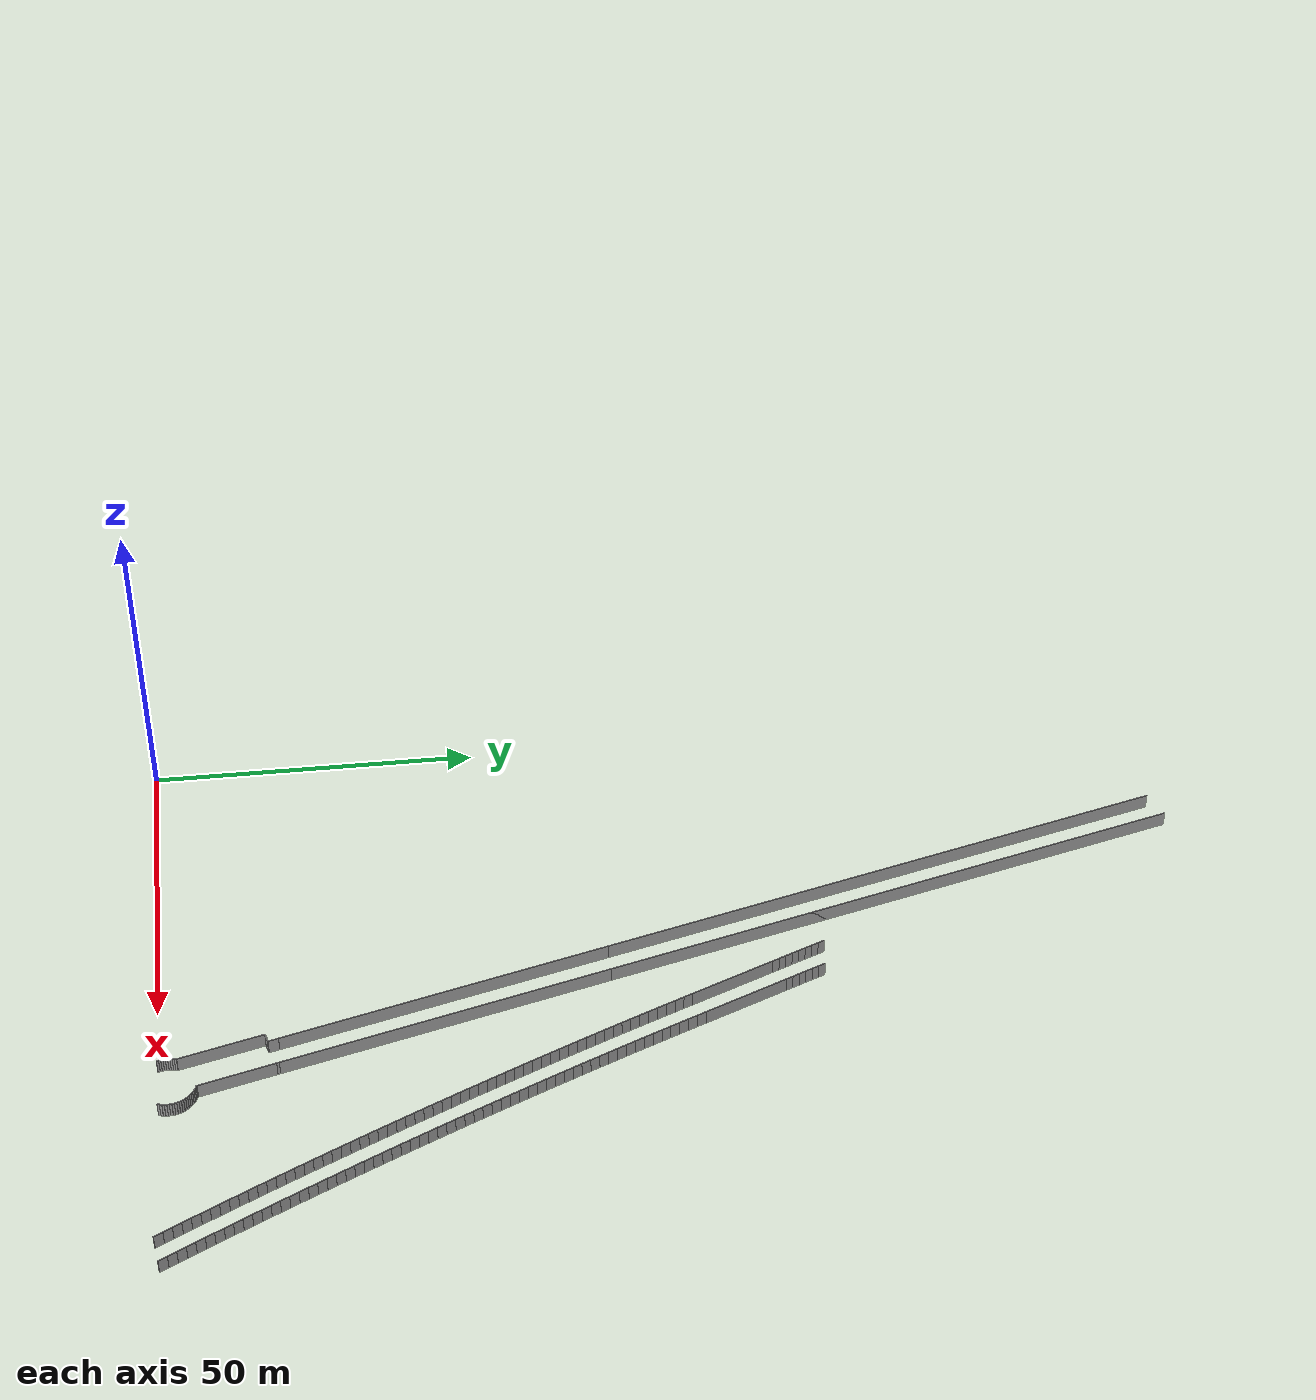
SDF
<?xml version="1.0" ?>
<sdf version="1.6">
  <model name="sps_0207">
    <pose frame="">0 0 0 0 -0 0</pose>
    <static>1</static>
    <self_collide>0</self_collide>
    <allow_auto_disable>0</allow_auto_disable>
    <link name="Wall269">
      <kinematic>0</kinematic>
      <gravity>1</gravity>
      <self_collide>0</self_collide>
      <collision name="collision">
        <geometry>
          <box>
            <size>13.7165 0.15 2.5</size>
          </box>
        </geometry>
        <pose frame="">0 0 0 0 -0 0</pose>
      </collision>
      <visual name="visual">
        <geometry>
          <box>
            <size>13.7165 0.15 2.5</size>
          </box>
        </geometry>
        <pose frame="">0 0 0 0 -0 0</pose>
        <cast_shadows>1</cast_shadows>
        <transparency>0.0</transparency>
      </visual>
      <pose frame="">53.6623 85.8426 1.25 0 0 -1.17761</pose>
    </link>
    <link name="Wall270">
      <kinematic>0</kinematic>
      <gravity>1</gravity>
      <self_collide>0</self_collide>
      <collision name="collision">
        <geometry>
          <box>
            <size>0.404023 0.15 2.5</size>
          </box>
        </geometry>
        <pose frame="">0 0 0 0 -0 0</pose>
      </collision>
      <visual name="visual">
        <geometry>
          <box>
            <size>0.404023 0.15 2.5</size>
          </box>
        </geometry>
        <pose frame="">0 0 0 0 -0 0</pose>
        <cast_shadows>1</cast_shadows>
        <transparency>0.0</transparency>
      </visual>
      <pose frame="">63.4606 17.6979 1.25 0 -0 1.83141</pose>
    </link>
    <link name="Wall271">
      <kinematic>0</kinematic>
      <gravity>1</gravity>
      <self_collide>0</self_collide>
      <collision name="collision">
        <geometry>
          <box>
            <size>51.7473 0.15 2.5</size>
          </box>
        </geometry>
        <pose frame="">0 0 0 0 -0 0</pose>
      </collision>
      <visual name="visual">
        <geometry>
          <box>
            <size>51.7473 0.15 2.5</size>
          </box>
        </geometry>
        <pose frame="">0 0 0 0 -0 0</pose>
        <cast_shadows>1</cast_shadows>
        <transparency>0.0</transparency>
      </visual>
      <pose frame="">56.7417 42.8931 1.25 0 -0 1.83141</pose>
    </link>
    <link name="Wall272">
      <kinematic>0</kinematic>
      <gravity>1</gravity>
      <self_collide>0</self_collide>
      <collision name="collision">
        <geometry>
          <box>
            <size>51.7473 0.15 2.5</size>
          </box>
        </geometry>
        <pose frame="">0 0 0 0 -0 0</pose>
      </collision>
      <visual name="visual">
        <geometry>
          <box>
            <size>51.7473 0.15 2.5</size>
          </box>
        </geometry>
        <pose frame="">0 0 0 0 -0 0</pose>
        <cast_shadows>1</cast_shadows>
        <transparency>0.0</transparency>
      </visual>
      <pose frame="">43.408 92.8931 1.25 0 -0 1.83141</pose>
    </link>
    <link name="Wall329">
      <kinematic>0</kinematic>
      <gravity>1</gravity>
      <self_collide>0</self_collide>
      <collision name="collision">
        <geometry>
          <box>
            <size>1.61069 0.15 2.5</size>
          </box>
        </geometry>
        <pose frame="">0 0 0 0 -0 0</pose>
      </collision>
      <visual name="visual">
        <geometry>
          <box>
            <size>1.61069 0.15 2.5</size>
          </box>
        </geometry>
        <pose frame="">0 0 0 0 -0 0</pose>
        <cast_shadows>1</cast_shadows>
        <transparency>0.0</transparency>
      </visual>
      <pose frame="">58.9327 17.1149 1.25 0 -0 1.83117</pose>
    </link>
    <link name="Wall330">
      <kinematic>0</kinematic>
      <gravity>1</gravity>
      <self_collide>0</self_collide>
      <collision name="collision">
        <geometry>
          <box>
            <size>51.7441 0.15 2.5</size>
          </box>
        </geometry>
        <pose frame="">0 0 0 0 -0 0</pose>
      </collision>
      <visual name="visual">
        <geometry>
          <box>
            <size>51.7441 0.15 2.5</size>
          </box>
        </geometry>
        <pose frame="">0 0 0 0 -0 0</pose>
        <cast_shadows>1</cast_shadows>
        <transparency>0.0</transparency>
      </visual>
      <pose frame="">52.0647 42.8931 1.25 0 -0 1.83117</pose>
    </link>
    <link name="Wall331">
      <kinematic>0</kinematic>
      <gravity>1</gravity>
      <self_collide>0</self_collide>
      <collision name="collision">
        <geometry>
          <box>
            <size>42.4736 0.15 2.5</size>
          </box>
        </geometry>
        <pose frame="">0 0 0 0 -0 0</pose>
      </collision>
      <visual name="visual">
        <geometry>
          <box>
            <size>42.4736 0.15 2.5</size>
          </box>
        </geometry>
        <pose frame="">0 0 0 0 -0 0</pose>
        <cast_shadows>1</cast_shadows>
        <transparency>0.0</transparency>
      </visual>
      <pose frame="">39.9368 88.414 1.25 0 -0 1.83117</pose>
    </link>
    <link name="Wall595">
      <kinematic>0</kinematic>
      <gravity>1</gravity>
      <self_collide>0</self_collide>
      <collision name="collision">
        <geometry>
          <box>
            <size>13.7266 0.15 2.5</size>
          </box>
        </geometry>
        <pose frame="">0 0 0 0 -0 0</pose>
      </collision>
      <visual name="visual">
        <geometry>
          <box>
            <size>13.7266 0.15 2.5</size>
          </box>
        </geometry>
        <pose frame="">0 0 0 0 -0 0</pose>
        <cast_shadows>1</cast_shadows>
        <transparency>0.0</transparency>
      </visual>
      <pose frame="">57.4856 87.4298 1.25 0 -0 1.96409</pose>
    </link>
    <link name="Wall1853">
      <kinematic>0</kinematic>
      <gravity>1</gravity>
      <self_collide>0</self_collide>
      <collision name="collision">
        <geometry>
          <box>
            <size>12.1005 0.15 2.5</size>
          </box>
        </geometry>
        <pose frame="">0 0 0 0 -0 0</pose>
      </collision>
      <visual name="visual">
        <geometry>
          <box>
            <size>12.1005 0.15 2.5</size>
          </box>
        </geometry>
        <pose frame="">0 0 0 0 -0 0</pose>
        <cast_shadows>1</cast_shadows>
        <transparency>0.0</transparency>
      </visual>
      <pose frame="">65.0825 11.6597 1.25 0 0 -1.30832</pose>
    </link>
    <link name="Wall1854">
      <kinematic>0</kinematic>
      <gravity>1</gravity>
      <self_collide>0</self_collide>
      <collision name="collision">
        <geometry>
          <box>
            <size>0.359052 0.15 2.5</size>
          </box>
        </geometry>
        <pose frame="">0 0 0 0 -0 0</pose>
      </collision>
      <visual name="visual">
        <geometry>
          <box>
            <size>0.359052 0.15 2.5</size>
          </box>
        </geometry>
        <pose frame="">0 0 0 0 -0 0</pose>
        <cast_shadows>1</cast_shadows>
        <transparency>0.0</transparency>
      </visual>
      <pose frame="">66.8222 5.75838 1.25 0 0 -0.330674</pose>
    </link>
    <link name="Wall1855">
      <kinematic>0</kinematic>
      <gravity>1</gravity>
      <self_collide>0</self_collide>
      <collision name="collision">
        <geometry>
          <box>
            <size>0.358996 0.15 2.5</size>
          </box>
        </geometry>
        <pose frame="">0 0 0 0 -0 0</pose>
      </collision>
      <visual name="visual">
        <geometry>
          <box>
            <size>0.358996 0.15 2.5</size>
          </box>
        </geometry>
        <pose frame="">0 0 0 0 -0 0</pose>
        <cast_shadows>1</cast_shadows>
        <transparency>0.0</transparency>
      </visual>
      <pose frame="">67.1565 5.6281 1.25 0 0 -0.412683</pose>
    </link>
    <link name="Wall1856">
      <kinematic>0</kinematic>
      <gravity>1</gravity>
      <self_collide>0</self_collide>
      <collision name="collision">
        <geometry>
          <box>
            <size>0.359076 0.15 2.5</size>
          </box>
        </geometry>
        <pose frame="">0 0 0 0 -0 0</pose>
      </collision>
      <visual name="visual">
        <geometry>
          <box>
            <size>0.359076 0.15 2.5</size>
          </box>
        </geometry>
        <pose frame="">0 0 0 0 -0 0</pose>
        <cast_shadows>1</cast_shadows>
        <transparency>0.0</transparency>
      </visual>
      <pose frame="">67.479 5.47099 1.25 0 0 -0.493907</pose>
    </link>
    <link name="Wall1857">
      <kinematic>0</kinematic>
      <gravity>1</gravity>
      <self_collide>0</self_collide>
      <collision name="collision">
        <geometry>
          <box>
            <size>0.359122 0.15 2.5</size>
          </box>
        </geometry>
        <pose frame="">0 0 0 0 -0 0</pose>
      </collision>
      <visual name="visual">
        <geometry>
          <box>
            <size>0.359122 0.15 2.5</size>
          </box>
        </geometry>
        <pose frame="">0 0 0 0 -0 0</pose>
        <cast_shadows>1</cast_shadows>
        <transparency>0.0</transparency>
      </visual>
      <pose frame="">67.7877 5.2881 1.25 0 0 -0.575841</pose>
    </link>
    <link name="Wall1858">
      <kinematic>0</kinematic>
      <gravity>1</gravity>
      <self_collide>0</self_collide>
      <collision name="collision">
        <geometry>
          <box>
            <size>0.35892 0.15 2.5</size>
          </box>
        </geometry>
        <pose frame="">0 0 0 0 -0 0</pose>
      </collision>
      <visual name="visual">
        <geometry>
          <box>
            <size>0.35892 0.15 2.5</size>
          </box>
        </geometry>
        <pose frame="">0 0 0 0 -0 0</pose>
        <cast_shadows>1</cast_shadows>
        <transparency>0.0</transparency>
      </visual>
      <pose frame="">68.0803 5.0807 1.25 0 0 -0.657106</pose>
    </link>
    <link name="Wall1859">
      <kinematic>0</kinematic>
      <gravity>1</gravity>
      <self_collide>0</self_collide>
      <collision name="collision">
        <geometry>
          <box>
            <size>0.359021 0.15 2.5</size>
          </box>
        </geometry>
        <pose frame="">0 0 0 0 -0 0</pose>
      </collision>
      <visual name="visual">
        <geometry>
          <box>
            <size>0.359021 0.15 2.5</size>
          </box>
        </geometry>
        <pose frame="">0 0 0 0 -0 0</pose>
        <cast_shadows>1</cast_shadows>
        <transparency>0.0</transparency>
      </visual>
      <pose frame="">68.355 4.85008 1.25 0 0 -0.739702</pose>
    </link>
    <link name="Wall1860">
      <kinematic>0</kinematic>
      <gravity>1</gravity>
      <self_collide>0</self_collide>
      <collision name="collision">
        <geometry>
          <box>
            <size>0.358995 0.15 2.5</size>
          </box>
        </geometry>
        <pose frame="">0 0 0 0 -0 0</pose>
      </collision>
      <visual name="visual">
        <geometry>
          <box>
            <size>0.358995 0.15 2.5</size>
          </box>
        </geometry>
        <pose frame="">0 0 0 0 -0 0</pose>
        <cast_shadows>1</cast_shadows>
        <transparency>0.0</transparency>
      </visual>
      <pose frame="">68.61 4.59779 1.25 0 0 -0.820389</pose>
    </link>
    <link name="Wall1861">
      <kinematic>0</kinematic>
      <gravity>1</gravity>
      <self_collide>0</self_collide>
      <collision name="collision">
        <geometry>
          <box>
            <size>0.359109 0.15 2.5</size>
          </box>
        </geometry>
        <pose frame="">0 0 0 0 -0 0</pose>
      </collision>
      <visual name="visual">
        <geometry>
          <box>
            <size>0.359109 0.15 2.5</size>
          </box>
        </geometry>
        <pose frame="">0 0 0 0 -0 0</pose>
        <cast_shadows>1</cast_shadows>
        <transparency>0.0</transparency>
      </visual>
      <pose frame="">68.8437 4.32561 1.25 0 0 -0.90224</pose>
    </link>
    <link name="Wall1862">
      <kinematic>0</kinematic>
      <gravity>1</gravity>
      <self_collide>0</self_collide>
      <collision name="collision">
        <geometry>
          <box>
            <size>0.359062 0.15 2.5</size>
          </box>
        </geometry>
        <pose frame="">0 0 0 0 -0 0</pose>
      </collision>
      <visual name="visual">
        <geometry>
          <box>
            <size>0.359062 0.15 2.5</size>
          </box>
        </geometry>
        <pose frame="">0 0 0 0 -0 0</pose>
        <cast_shadows>1</cast_shadows>
        <transparency>0.0</transparency>
      </visual>
      <pose frame="">69.0544 4.0352 1.25 0 0 -0.984067</pose>
    </link>
    <link name="Wall1863">
      <kinematic>0</kinematic>
      <gravity>1</gravity>
      <self_collide>0</self_collide>
      <collision name="collision">
        <geometry>
          <box>
            <size>0.358927 0.15 2.5</size>
          </box>
        </geometry>
        <pose frame="">0 0 0 0 -0 0</pose>
      </collision>
      <visual name="visual">
        <geometry>
          <box>
            <size>0.358927 0.15 2.5</size>
          </box>
        </geometry>
        <pose frame="">0 0 0 0 -0 0</pose>
        <cast_shadows>1</cast_shadows>
        <transparency>0.0</transparency>
      </visual>
      <pose frame="">69.2407 3.72868 1.25 0 0 -1.06523</pose>
    </link>
    <link name="Wall1864">
      <kinematic>0</kinematic>
      <gravity>1</gravity>
      <self_collide>0</self_collide>
      <collision name="collision">
        <geometry>
          <box>
            <size>0.359119 0.15 2.5</size>
          </box>
        </geometry>
        <pose frame="">0 0 0 0 -0 0</pose>
      </collision>
      <visual name="visual">
        <geometry>
          <box>
            <size>0.359119 0.15 2.5</size>
          </box>
        </geometry>
        <pose frame="">0 0 0 0 -0 0</pose>
        <cast_shadows>1</cast_shadows>
        <transparency>0.0</transparency>
      </visual>
      <pose frame="">69.4015 3.40797 1.25 0 0 -1.14729</pose>
    </link>
    <link name="Wall1865">
      <kinematic>0</kinematic>
      <gravity>1</gravity>
      <self_collide>0</self_collide>
      <collision name="collision">
        <geometry>
          <box>
            <size>0.359057 0.15 2.5</size>
          </box>
        </geometry>
        <pose frame="">0 0 0 0 -0 0</pose>
      </collision>
      <visual name="visual">
        <geometry>
          <box>
            <size>0.359057 0.15 2.5</size>
          </box>
        </geometry>
        <pose frame="">0 0 0 0 -0 0</pose>
        <cast_shadows>1</cast_shadows>
        <transparency>0.0</transparency>
      </visual>
      <pose frame="">69.5355 3.07518 1.25 0 0 -1.22824</pose>
    </link>
    <link name="Wall1866">
      <kinematic>0</kinematic>
      <gravity>1</gravity>
      <self_collide>0</self_collide>
      <collision name="collision">
        <geometry>
          <box>
            <size>0.359079 0.15 2.5</size>
          </box>
        </geometry>
        <pose frame="">0 0 0 0 -0 0</pose>
      </collision>
      <visual name="visual">
        <geometry>
          <box>
            <size>0.359079 0.15 2.5</size>
          </box>
        </geometry>
        <pose frame="">0 0 0 0 -0 0</pose>
        <cast_shadows>1</cast_shadows>
        <transparency>0.0</transparency>
      </visual>
      <pose frame="">69.6421 2.73259 1.25 0 0 -1.31052</pose>
    </link>
    <link name="Wall1867">
      <kinematic>0</kinematic>
      <gravity>1</gravity>
      <self_collide>0</self_collide>
      <collision name="collision">
        <geometry>
          <box>
            <size>0.359147 0.15 2.5</size>
          </box>
        </geometry>
        <pose frame="">0 0 0 0 -0 0</pose>
      </collision>
      <visual name="visual">
        <geometry>
          <box>
            <size>0.359147 0.15 2.5</size>
          </box>
        </geometry>
        <pose frame="">0 0 0 0 -0 0</pose>
        <cast_shadows>1</cast_shadows>
        <transparency>0.0</transparency>
      </visual>
      <pose frame="">69.7203 2.3824 1.25 0 0 -1.39157</pose>
    </link>
    <link name="Wall1868">
      <kinematic>0</kinematic>
      <gravity>1</gravity>
      <self_collide>0</self_collide>
      <collision name="collision">
        <geometry>
          <box>
            <size>0.359111 0.15 2.5</size>
          </box>
        </geometry>
        <pose frame="">0 0 0 0 -0 0</pose>
      </collision>
      <visual name="visual">
        <geometry>
          <box>
            <size>0.359111 0.15 2.5</size>
          </box>
        </geometry>
        <pose frame="">0 0 0 0 -0 0</pose>
        <cast_shadows>1</cast_shadows>
        <transparency>0.0</transparency>
      </visual>
      <pose frame="">69.7697 2.02699 1.25 0 0 -1.47377</pose>
    </link>
    <link name="Wall1869">
      <kinematic>0</kinematic>
      <gravity>1</gravity>
      <self_collide>0</self_collide>
      <collision name="collision">
        <geometry>
          <box>
            <size>0.359053 0.15 2.5</size>
          </box>
        </geometry>
        <pose frame="">0 0 0 0 -0 0</pose>
      </collision>
      <visual name="visual">
        <geometry>
          <box>
            <size>0.359053 0.15 2.5</size>
          </box>
        </geometry>
        <pose frame="">0 0 0 0 -0 0</pose>
        <cast_shadows>1</cast_shadows>
        <transparency>0.0</transparency>
      </visual>
      <pose frame="">69.7899 1.66878 1.25 0 0 -1.55516</pose>
    </link>
    <link name="Wall1870">
      <kinematic>0</kinematic>
      <gravity>1</gravity>
      <self_collide>0</self_collide>
      <collision name="collision">
        <geometry>
          <box>
            <size>0.358944 0.15 2.5</size>
          </box>
        </geometry>
        <pose frame="">0 0 0 0 -0 0</pose>
      </collision>
      <visual name="visual">
        <geometry>
          <box>
            <size>0.358944 0.15 2.5</size>
          </box>
        </geometry>
        <pose frame="">0 0 0 0 -0 0</pose>
        <cast_shadows>1</cast_shadows>
        <transparency>0.0</transparency>
      </visual>
      <pose frame="">69.7808 1.31019 1.25 0 0 -1.63716</pose>
    </link>
    <link name="Wall1871">
      <kinematic>0</kinematic>
      <gravity>1</gravity>
      <self_collide>0</self_collide>
      <collision name="collision">
        <geometry>
          <box>
            <size>0.359136 0.15 2.5</size>
          </box>
        </geometry>
        <pose frame="">0 0 0 0 -0 0</pose>
      </collision>
      <visual name="visual">
        <geometry>
          <box>
            <size>0.359136 0.15 2.5</size>
          </box>
        </geometry>
        <pose frame="">0 0 0 0 -0 0</pose>
        <cast_shadows>1</cast_shadows>
        <transparency>0.0</transparency>
      </visual>
      <pose frame="">69.7425 0.953505 1.25 0 0 -1.71851</pose>
    </link>
    <link name="Wall1872">
      <kinematic>0</kinematic>
      <gravity>1</gravity>
      <self_collide>0</self_collide>
      <collision name="collision">
        <geometry>
          <box>
            <size>0.358993 0.15 2.5</size>
          </box>
        </geometry>
        <pose frame="">0 0 0 0 -0 0</pose>
      </collision>
      <visual name="visual">
        <geometry>
          <box>
            <size>0.358993 0.15 2.5</size>
          </box>
        </geometry>
        <pose frame="">0 0 0 0 -0 0</pose>
        <cast_shadows>1</cast_shadows>
        <transparency>0.0</transparency>
      </visual>
      <pose frame="">69.6753 0.601088 1.25 0 0 -1.79994</pose>
    </link>
    <link name="Wall1873">
      <kinematic>0</kinematic>
      <gravity>1</gravity>
      <self_collide>0</self_collide>
      <collision name="collision">
        <geometry>
          <box>
            <size>0.359076 0.15 2.5</size>
          </box>
        </geometry>
        <pose frame="">0 0 0 0 -0 0</pose>
      </collision>
      <visual name="visual">
        <geometry>
          <box>
            <size>0.359076 0.15 2.5</size>
          </box>
        </geometry>
        <pose frame="">0 0 0 0 -0 0</pose>
        <cast_shadows>1</cast_shadows>
        <transparency>0.0</transparency>
      </visual>
      <pose frame="">69.5795 0.255385 1.25 0 0 -1.88228</pose>
    </link>
    <link name="Wall1900">
      <kinematic>0</kinematic>
      <gravity>1</gravity>
      <self_collide>0</self_collide>
      <collision name="collision">
        <geometry>
          <box>
            <size>0.335259 0.15 2.5</size>
          </box>
        </geometry>
        <pose frame="">0 0 0 0 -0 0</pose>
      </collision>
      <visual name="visual">
        <geometry>
          <box>
            <size>0.335259 0.15 2.5</size>
          </box>
        </geometry>
        <pose frame="">0 0 0 0 -0 0</pose>
        <cast_shadows>1</cast_shadows>
        <transparency>0.0</transparency>
      </visual>
      <pose frame="">61.2461 0.148513 1.25 0 -0 1.90775</pose>
    </link>
    <link name="Wall1901">
      <kinematic>0</kinematic>
      <gravity>1</gravity>
      <self_collide>0</self_collide>
      <collision name="collision">
        <geometry>
          <box>
            <size>0.335064 0.15 2.5</size>
          </box>
        </geometry>
        <pose frame="">0 0 0 0 -0 0</pose>
      </collision>
      <visual name="visual">
        <geometry>
          <box>
            <size>0.335064 0.15 2.5</size>
          </box>
        </geometry>
        <pose frame="">0 0 0 0 -0 0</pose>
        <cast_shadows>1</cast_shadows>
        <transparency>0.0</transparency>
      </visual>
      <pose frame="">61.1475 0.468612 1.25 0 -0 1.83093</pose>
    </link>
    <link name="Wall1902">
      <kinematic>0</kinematic>
      <gravity>1</gravity>
      <self_collide>0</self_collide>
      <collision name="collision">
        <geometry>
          <box>
            <size>0.33526 0.15 2.5</size>
          </box>
        </geometry>
        <pose frame="">0 0 0 0 -0 0</pose>
      </collision>
      <visual name="visual">
        <geometry>
          <box>
            <size>0.33526 0.15 2.5</size>
          </box>
        </geometry>
        <pose frame="">0 0 0 0 -0 0</pose>
        <cast_shadows>1</cast_shadows>
        <transparency>0.0</transparency>
      </visual>
      <pose frame="">61.0738 0.795302 1.25 0 -0 1.75498</pose>
    </link>
    <link name="Wall1903">
      <kinematic>0</kinematic>
      <gravity>1</gravity>
      <self_collide>0</self_collide>
      <collision name="collision">
        <geometry>
          <box>
            <size>0.335131 0.15 2.5</size>
          </box>
        </geometry>
        <pose frame="">0 0 0 0 -0 0</pose>
      </collision>
      <visual name="visual">
        <geometry>
          <box>
            <size>0.335131 0.15 2.5</size>
          </box>
        </geometry>
        <pose frame="">0 0 0 0 -0 0</pose>
        <cast_shadows>1</cast_shadows>
        <transparency>0.0</transparency>
      </visual>
      <pose frame="">61.025 1.12669 1.25 0 -0 1.67846</pose>
    </link>
    <link name="Wall1904">
      <kinematic>0</kinematic>
      <gravity>1</gravity>
      <self_collide>0</self_collide>
      <collision name="collision">
        <geometry>
          <box>
            <size>0.335379 0.15 2.5</size>
          </box>
        </geometry>
        <pose frame="">0 0 0 0 -0 0</pose>
      </collision>
      <visual name="visual">
        <geometry>
          <box>
            <size>0.335379 0.15 2.5</size>
          </box>
        </geometry>
        <pose frame="">0 0 0 0 -0 0</pose>
        <cast_shadows>1</cast_shadows>
        <transparency>0.0</transparency>
      </visual>
      <pose frame="">61.0016 1.46089 1.25 0 -0 1.60301</pose>
    </link>
    <link name="Wall1905">
      <kinematic>0</kinematic>
      <gravity>1</gravity>
      <self_collide>0</self_collide>
      <collision name="collision">
        <geometry>
          <box>
            <size>0.335114 0.15 2.5</size>
          </box>
        </geometry>
        <pose frame="">0 0 0 0 -0 0</pose>
      </collision>
      <visual name="visual">
        <geometry>
          <box>
            <size>0.335114 0.15 2.5</size>
          </box>
        </geometry>
        <pose frame="">0 0 0 0 -0 0</pose>
        <cast_shadows>1</cast_shadows>
        <transparency>0.0</transparency>
      </visual>
      <pose frame="">61.0037 1.79588 1.25 0 -0 1.52598</pose>
    </link>
    <link name="Wall1906">
      <kinematic>0</kinematic>
      <gravity>1</gravity>
      <self_collide>0</self_collide>
      <collision name="collision">
        <geometry>
          <box>
            <size>0.335268 0.15 2.5</size>
          </box>
        </geometry>
        <pose frame="">0 0 0 0 -0 0</pose>
      </collision>
      <visual name="visual">
        <geometry>
          <box>
            <size>0.335268 0.15 2.5</size>
          </box>
        </geometry>
        <pose frame="">0 0 0 0 -0 0</pose>
        <cast_shadows>1</cast_shadows>
        <transparency>0.0</transparency>
      </visual>
      <pose frame="">61.0315 2.12968 1.25 0 -0 1.44999</pose>
    </link>
    <link name="Wall1907">
      <kinematic>0</kinematic>
      <gravity>1</gravity>
      <self_collide>0</self_collide>
      <collision name="collision">
        <geometry>
          <box>
            <size>0.335279 0.15 2.5</size>
          </box>
        </geometry>
        <pose frame="">0 0 0 0 -0 0</pose>
      </collision>
      <visual name="visual">
        <geometry>
          <box>
            <size>0.335279 0.15 2.5</size>
          </box>
        </geometry>
        <pose frame="">0 0 0 0 -0 0</pose>
        <cast_shadows>1</cast_shadows>
        <transparency>0.0</transparency>
      </visual>
      <pose frame="">61.0845 2.46049 1.25 0 -0 1.37383</pose>
    </link>
    <link name="Wall1908">
      <kinematic>0</kinematic>
      <gravity>1</gravity>
      <self_collide>0</self_collide>
      <collision name="collision">
        <geometry>
          <box>
            <size>0.335232 0.15 2.5</size>
          </box>
        </geometry>
        <pose frame="">0 0 0 0 -0 0</pose>
      </collision>
      <visual name="visual">
        <geometry>
          <box>
            <size>0.335232 0.15 2.5</size>
          </box>
        </geometry>
        <pose frame="">0 0 0 0 -0 0</pose>
        <cast_shadows>1</cast_shadows>
        <transparency>0.0</transparency>
      </visual>
      <pose frame="">61.1625 2.7863 1.25 0 -0 1.29777</pose>
    </link>
    <link name="Wall1909">
      <kinematic>0</kinematic>
      <gravity>1</gravity>
      <self_collide>0</self_collide>
      <collision name="collision">
        <geometry>
          <box>
            <size>13.4709 0.15 2.5</size>
          </box>
        </geometry>
        <pose frame="">0 0 0 0 -0 0</pose>
      </collision>
      <visual name="visual">
        <geometry>
          <box>
            <size>13.4709 0.15 2.5</size>
          </box>
        </geometry>
        <pose frame="">0 0 0 0 -0 0</pose>
        <cast_shadows>1</cast_shadows>
        <transparency>0.0</transparency>
      </visual>
      <pose frame="">59.4733 9.45601 1.25 0 -0 1.83123</pose>
    </link>
    <link name="Wall1910">
      <kinematic>0</kinematic>
      <gravity>1</gravity>
      <self_collide>0</self_collide>
      <collision name="collision">
        <geometry>
          <box>
            <size>1.44982 0.15 2.5</size>
          </box>
        </geometry>
        <pose frame="">0 0 0 0 -0 0</pose>
      </collision>
      <visual name="visual">
        <geometry>
          <box>
            <size>1.44982 0.15 2.5</size>
          </box>
        </geometry>
        <pose frame="">0 0 0 0 -0 0</pose>
        <cast_shadows>1</cast_shadows>
        <transparency>0.0</transparency>
      </visual>
      <pose frame="">58.4394 16.1505 1.25 0 -0 0.259754</pose>
    </link>
    <link name="Wall1911">
      <kinematic>0</kinematic>
      <gravity>1</gravity>
      <self_collide>0</self_collide>
      <collision name="collision">
        <geometry>
          <box>
            <size>143.64 0.15 2.5</size>
          </box>
        </geometry>
        <pose frame="">0 0 0 0 -0 0</pose>
      </collision>
      <visual name="visual">
        <geometry>
          <box>
            <size>143.64 0.15 2.5</size>
          </box>
        </geometry>
        <pose frame="">0 0 0 0 -0 0</pose>
        <cast_shadows>1</cast_shadows>
        <transparency>0.0</transparency>
      </visual>
      <pose frame="">40.6503 85.736 1.25 0 -0 1.83117</pose>
    </link>
    <link name="Wall1915">
      <kinematic>0</kinematic>
      <gravity>1</gravity>
      <self_collide>0</self_collide>
      <collision name="collision">
        <geometry>
          <box>
            <size>144.519 0.15 2.5</size>
          </box>
        </geometry>
        <pose frame="">0 0 0 0 -0 0</pose>
      </collision>
      <visual name="visual">
        <geometry>
          <box>
            <size>144.519 0.15 2.5</size>
          </box>
        </geometry>
        <pose frame="">0 0 0 0 -0 0</pose>
        <cast_shadows>1</cast_shadows>
        <transparency>0.0</transparency>
      </visual>
      <pose frame="">44.8935 87.3223 1.25 0 0 -1.31019</pose>
    </link>
    <link name="Wall4785">
      <kinematic>0</kinematic>
      <gravity>1</gravity>
      <self_collide>0</self_collide>
      <collision name="collision">
        <geometry>
          <box>
            <size>1.12142 0.15 2.5</size>
          </box>
        </geometry>
        <pose frame="">0 0 0 0 -0 0</pose>
      </collision>
      <visual name="visual">
        <geometry>
          <box>
            <size>1.12142 0.15 2.5</size>
          </box>
        </geometry>
        <pose frame="">0 0 0 0 -0 0</pose>
        <cast_shadows>1</cast_shadows>
        <transparency>0.0</transparency>
      </visual>
      <pose frame="">52.5029 99.4705 1.25 0 0 -1.1827</pose>
    </link>
    <link name="Wall4786">
      <kinematic>0</kinematic>
      <gravity>1</gravity>
      <self_collide>0</self_collide>
      <collision name="collision">
        <geometry>
          <box>
            <size>1.12149 0.15 2.5</size>
          </box>
        </geometry>
        <pose frame="">0 0 0 0 -0 0</pose>
      </collision>
      <visual name="visual">
        <geometry>
          <box>
            <size>1.12149 0.15 2.5</size>
          </box>
        </geometry>
        <pose frame="">0 0 0 0 -0 0</pose>
        <cast_shadows>1</cast_shadows>
        <transparency>0.0</transparency>
      </visual>
      <pose frame="">52.9278 98.4327 1.25 0 0 -1.18155</pose>
    </link>
    <link name="Wall4787">
      <kinematic>0</kinematic>
      <gravity>1</gravity>
      <self_collide>0</self_collide>
      <collision name="collision">
        <geometry>
          <box>
            <size>1.12122 0.15 2.5</size>
          </box>
        </geometry>
        <pose frame="">0 0 0 0 -0 0</pose>
      </collision>
      <visual name="visual">
        <geometry>
          <box>
            <size>1.12122 0.15 2.5</size>
          </box>
        </geometry>
        <pose frame="">0 0 0 0 -0 0</pose>
        <cast_shadows>1</cast_shadows>
        <transparency>0.0</transparency>
      </visual>
      <pose frame="">53.3541 97.3955 1.25 0 0 -1.18027</pose>
    </link>
    <link name="Wall4788">
      <kinematic>0</kinematic>
      <gravity>1</gravity>
      <self_collide>0</self_collide>
      <collision name="collision">
        <geometry>
          <box>
            <size>1.12156 0.15 2.5</size>
          </box>
        </geometry>
        <pose frame="">0 0 0 0 -0 0</pose>
      </collision>
      <visual name="visual">
        <geometry>
          <box>
            <size>1.12156 0.15 2.5</size>
          </box>
        </geometry>
        <pose frame="">0 0 0 0 -0 0</pose>
        <cast_shadows>1</cast_shadows>
        <transparency>0.0</transparency>
      </visual>
      <pose frame="">53.7815 96.3588 1.25 0 0 -1.1791</pose>
    </link>
    <link name="Wall4789">
      <kinematic>0</kinematic>
      <gravity>1</gravity>
      <self_collide>0</self_collide>
      <collision name="collision">
        <geometry>
          <box>
            <size>1.12134 0.15 2.5</size>
          </box>
        </geometry>
        <pose frame="">0 0 0 0 -0 0</pose>
      </collision>
      <visual name="visual">
        <geometry>
          <box>
            <size>1.12134 0.15 2.5</size>
          </box>
        </geometry>
        <pose frame="">0 0 0 0 -0 0</pose>
        <cast_shadows>1</cast_shadows>
        <transparency>0.0</transparency>
      </visual>
      <pose frame="">54.2102 95.3225 1.25 0 0 -1.17802</pose>
    </link>
    <link name="Wall4790">
      <kinematic>0</kinematic>
      <gravity>1</gravity>
      <self_collide>0</self_collide>
      <collision name="collision">
        <geometry>
          <box>
            <size>1.12137 0.15 2.5</size>
          </box>
        </geometry>
        <pose frame="">0 0 0 0 -0 0</pose>
      </collision>
      <visual name="visual">
        <geometry>
          <box>
            <size>1.12137 0.15 2.5</size>
          </box>
        </geometry>
        <pose frame="">0 0 0 0 -0 0</pose>
        <cast_shadows>1</cast_shadows>
        <transparency>0.0</transparency>
      </visual>
      <pose frame="">54.6401 94.2868 1.25 0 0 -1.17668</pose>
    </link>
    <link name="Wall8304">
      <kinematic>0</kinematic>
      <gravity>1</gravity>
      <self_collide>0</self_collide>
      <collision name="collision">
        <geometry>
          <box>
            <size>1.49891 0.15 2.5</size>
          </box>
        </geometry>
        <pose frame="">0 0 0 0 -0 0</pose>
      </collision>
      <visual name="visual">
        <geometry>
          <box>
            <size>1.49891 0.15 2.5</size>
          </box>
        </geometry>
        <pose frame="">0 0 0 0 -0 0</pose>
        <cast_shadows>1</cast_shadows>
        <transparency>0.0</transparency>
      </visual>
      <pose frame="">56.577 78.8154 1.25 0 0 -1.1777</pose>
    </link>
    <link name="Wall8305">
      <kinematic>0</kinematic>
      <gravity>1</gravity>
      <self_collide>0</self_collide>
      <collision name="collision">
        <geometry>
          <box>
            <size>1.49903 0.15 2.5</size>
          </box>
        </geometry>
        <pose frame="">0 0 0 0 -0 0</pose>
      </collision>
      <visual name="visual">
        <geometry>
          <box>
            <size>1.49903 0.15 2.5</size>
          </box>
        </geometry>
        <pose frame="">0 0 0 0 -0 0</pose>
        <cast_shadows>1</cast_shadows>
        <transparency>0.0</transparency>
      </visual>
      <pose frame="">57.1522 77.4312 1.25 0 0 -1.17623</pose>
    </link>
    <link name="Wall8306">
      <kinematic>0</kinematic>
      <gravity>1</gravity>
      <self_collide>0</self_collide>
      <collision name="collision">
        <geometry>
          <box>
            <size>1.49916 0.15 2.5</size>
          </box>
        </geometry>
        <pose frame="">0 0 0 0 -0 0</pose>
      </collision>
      <visual name="visual">
        <geometry>
          <box>
            <size>1.49916 0.15 2.5</size>
          </box>
        </geometry>
        <pose frame="">0 0 0 0 -0 0</pose>
        <cast_shadows>1</cast_shadows>
        <transparency>0.0</transparency>
      </visual>
      <pose frame="">57.7296 76.0478 1.25 0 0 -1.17455</pose>
    </link>
    <link name="Wall8307">
      <kinematic>0</kinematic>
      <gravity>1</gravity>
      <self_collide>0</self_collide>
      <collision name="collision">
        <geometry>
          <box>
            <size>1.49886 0.15 2.5</size>
          </box>
        </geometry>
        <pose frame="">0 0 0 0 -0 0</pose>
      </collision>
      <visual name="visual">
        <geometry>
          <box>
            <size>1.49886 0.15 2.5</size>
          </box>
        </geometry>
        <pose frame="">0 0 0 0 -0 0</pose>
        <cast_shadows>1</cast_shadows>
        <transparency>0.0</transparency>
      </visual>
      <pose frame="">58.3093 74.6654 1.25 0 0 -1.17292</pose>
    </link>
    <link name="Wall8308">
      <kinematic>0</kinematic>
      <gravity>1</gravity>
      <self_collide>0</self_collide>
      <collision name="collision">
        <geometry>
          <box>
            <size>1.49916 0.15 2.5</size>
          </box>
        </geometry>
        <pose frame="">0 0 0 0 -0 0</pose>
      </collision>
      <visual name="visual">
        <geometry>
          <box>
            <size>1.49916 0.15 2.5</size>
          </box>
        </geometry>
        <pose frame="">0 0 0 0 -0 0</pose>
        <cast_shadows>1</cast_shadows>
        <transparency>0.0</transparency>
      </visual>
      <pose frame="">58.891 73.2839 1.25 0 0 -1.1715</pose>
    </link>
    <link name="Wall8309">
      <kinematic>0</kinematic>
      <gravity>1</gravity>
      <self_collide>0</self_collide>
      <collision name="collision">
        <geometry>
          <box>
            <size>1.49879 0.15 2.5</size>
          </box>
        </geometry>
        <pose frame="">0 0 0 0 -0 0</pose>
      </collision>
      <visual name="visual">
        <geometry>
          <box>
            <size>1.49879 0.15 2.5</size>
          </box>
        </geometry>
        <pose frame="">0 0 0 0 -0 0</pose>
        <cast_shadows>1</cast_shadows>
        <transparency>0.0</transparency>
      </visual>
      <pose frame="">59.4748 71.9033 1.25 0 0 -1.16998</pose>
    </link>
    <link name="Wall8310">
      <kinematic>0</kinematic>
      <gravity>1</gravity>
      <self_collide>0</self_collide>
      <collision name="collision">
        <geometry>
          <box>
            <size>1.49896 0.15 2.5</size>
          </box>
        </geometry>
        <pose frame="">0 0 0 0 -0 0</pose>
      </collision>
      <visual name="visual">
        <geometry>
          <box>
            <size>1.49896 0.15 2.5</size>
          </box>
        </geometry>
        <pose frame="">0 0 0 0 -0 0</pose>
        <cast_shadows>1</cast_shadows>
        <transparency>0.0</transparency>
      </visual>
      <pose frame="">60.0608 70.5237 1.25 0 0 -1.16826</pose>
    </link>
    <link name="Wall8311">
      <kinematic>0</kinematic>
      <gravity>1</gravity>
      <self_collide>0</self_collide>
      <collision name="collision">
        <geometry>
          <box>
            <size>1.49898 0.15 2.5</size>
          </box>
        </geometry>
        <pose frame="">0 0 0 0 -0 0</pose>
      </collision>
      <visual name="visual">
        <geometry>
          <box>
            <size>1.49898 0.15 2.5</size>
          </box>
        </geometry>
        <pose frame="">0 0 0 0 -0 0</pose>
        <cast_shadows>1</cast_shadows>
        <transparency>0.0</transparency>
      </visual>
      <pose frame="">60.6492 69.145 1.25 0 0 -1.16667</pose>
    </link>
    <link name="Wall8312">
      <kinematic>0</kinematic>
      <gravity>1</gravity>
      <self_collide>0</self_collide>
      <collision name="collision">
        <geometry>
          <box>
            <size>1.49896 0.15 2.5</size>
          </box>
        </geometry>
        <pose frame="">0 0 0 0 -0 0</pose>
      </collision>
      <visual name="visual">
        <geometry>
          <box>
            <size>1.49896 0.15 2.5</size>
          </box>
        </geometry>
        <pose frame="">0 0 0 0 -0 0</pose>
        <cast_shadows>1</cast_shadows>
        <transparency>0.0</transparency>
      </visual>
      <pose frame="">61.2396 67.7672 1.25 0 0 -1.16525</pose>
    </link>
    <link name="Wall8313">
      <kinematic>0</kinematic>
      <gravity>1</gravity>
      <self_collide>0</self_collide>
      <collision name="collision">
        <geometry>
          <box>
            <size>1.49886 0.15 2.5</size>
          </box>
        </geometry>
        <pose frame="">0 0 0 0 -0 0</pose>
      </collision>
      <visual name="visual">
        <geometry>
          <box>
            <size>1.49886 0.15 2.5</size>
          </box>
        </geometry>
        <pose frame="">0 0 0 0 -0 0</pose>
        <cast_shadows>1</cast_shadows>
        <transparency>0.0</transparency>
      </visual>
      <pose frame="">61.8321 66.3904 1.25 0 0 -1.16345</pose>
    </link>
    <link name="Wall8314">
      <kinematic>0</kinematic>
      <gravity>1</gravity>
      <self_collide>0</self_collide>
      <collision name="collision">
        <geometry>
          <box>
            <size>1.49888 0.15 2.5</size>
          </box>
        </geometry>
        <pose frame="">0 0 0 0 -0 0</pose>
      </collision>
      <visual name="visual">
        <geometry>
          <box>
            <size>1.49888 0.15 2.5</size>
          </box>
        </geometry>
        <pose frame="">0 0 0 0 -0 0</pose>
        <cast_shadows>1</cast_shadows>
        <transparency>0.0</transparency>
      </visual>
      <pose frame="">62.427 65.0146 1.25 0 0 -1.16199</pose>
    </link>
    <link name="Wall8315">
      <kinematic>0</kinematic>
      <gravity>1</gravity>
      <self_collide>0</self_collide>
      <collision name="collision">
        <geometry>
          <box>
            <size>1.49899 0.15 2.5</size>
          </box>
        </geometry>
        <pose frame="">0 0 0 0 -0 0</pose>
      </collision>
      <visual name="visual">
        <geometry>
          <box>
            <size>1.49899 0.15 2.5</size>
          </box>
        </geometry>
        <pose frame="">0 0 0 0 -0 0</pose>
        <cast_shadows>1</cast_shadows>
        <transparency>0.0</transparency>
      </visual>
      <pose frame="">63.024 63.6397 1.25 0 0 -1.16029</pose>
    </link>
    <link name="Wall8316">
      <kinematic>0</kinematic>
      <gravity>1</gravity>
      <self_collide>0</self_collide>
      <collision name="collision">
        <geometry>
          <box>
            <size>1.49899 0.15 2.5</size>
          </box>
        </geometry>
        <pose frame="">0 0 0 0 -0 0</pose>
      </collision>
      <visual name="visual">
        <geometry>
          <box>
            <size>1.49899 0.15 2.5</size>
          </box>
        </geometry>
        <pose frame="">0 0 0 0 -0 0</pose>
        <cast_shadows>1</cast_shadows>
        <transparency>0.0</transparency>
      </visual>
      <pose frame="">63.6232 62.2657 1.25 0 0 -1.15887</pose>
    </link>
    <link name="Wall8317">
      <kinematic>0</kinematic>
      <gravity>1</gravity>
      <self_collide>0</self_collide>
      <collision name="collision">
        <geometry>
          <box>
            <size>1.49894 0.15 2.5</size>
          </box>
        </geometry>
        <pose frame="">0 0 0 0 -0 0</pose>
      </collision>
      <visual name="visual">
        <geometry>
          <box>
            <size>1.49894 0.15 2.5</size>
          </box>
        </geometry>
        <pose frame="">0 0 0 0 -0 0</pose>
        <cast_shadows>1</cast_shadows>
        <transparency>0.0</transparency>
      </visual>
      <pose frame="">64.2244 60.8926 1.25 0 0 -1.15721</pose>
    </link>
    <link name="Wall8318">
      <kinematic>0</kinematic>
      <gravity>1</gravity>
      <self_collide>0</self_collide>
      <collision name="collision">
        <geometry>
          <box>
            <size>1.49899 0.15 2.5</size>
          </box>
        </geometry>
        <pose frame="">0 0 0 0 -0 0</pose>
      </collision>
      <visual name="visual">
        <geometry>
          <box>
            <size>1.49899 0.15 2.5</size>
          </box>
        </geometry>
        <pose frame="">0 0 0 0 -0 0</pose>
        <cast_shadows>1</cast_shadows>
        <transparency>0.0</transparency>
      </visual>
      <pose frame="">64.828 59.5205 1.25 0 0 -1.15562</pose>
    </link>
    <link name="Wall8319">
      <kinematic>0</kinematic>
      <gravity>1</gravity>
      <self_collide>0</self_collide>
      <collision name="collision">
        <geometry>
          <box>
            <size>1.49926 0.15 2.5</size>
          </box>
        </geometry>
        <pose frame="">0 0 0 0 -0 0</pose>
      </collision>
      <visual name="visual">
        <geometry>
          <box>
            <size>1.49926 0.15 2.5</size>
          </box>
        </geometry>
        <pose frame="">0 0 0 0 -0 0</pose>
        <cast_shadows>1</cast_shadows>
        <transparency>0.0</transparency>
      </visual>
      <pose frame="">65.4337 58.1492 1.25 0 0 -1.1541</pose>
    </link>
    <link name="Wall8320">
      <kinematic>0</kinematic>
      <gravity>1</gravity>
      <self_collide>0</self_collide>
      <collision name="collision">
        <geometry>
          <box>
            <size>1.4989 0.15 2.5</size>
          </box>
        </geometry>
        <pose frame="">0 0 0 0 -0 0</pose>
      </collision>
      <visual name="visual">
        <geometry>
          <box>
            <size>1.4989 0.15 2.5</size>
          </box>
        </geometry>
        <pose frame="">0 0 0 0 -0 0</pose>
        <cast_shadows>1</cast_shadows>
        <transparency>0.0</transparency>
      </visual>
      <pose frame="">66.0416 56.7789 1.25 0 0 -1.15244</pose>
    </link>
    <link name="Wall8321">
      <kinematic>0</kinematic>
      <gravity>1</gravity>
      <self_collide>0</self_collide>
      <collision name="collision">
        <geometry>
          <box>
            <size>1.49896 0.15 2.5</size>
          </box>
        </geometry>
        <pose frame="">0 0 0 0 -0 0</pose>
      </collision>
      <visual name="visual">
        <geometry>
          <box>
            <size>1.49896 0.15 2.5</size>
          </box>
        </geometry>
        <pose frame="">0 0 0 0 -0 0</pose>
        <cast_shadows>1</cast_shadows>
        <transparency>0.0</transparency>
      </visual>
      <pose frame="">66.6515 55.4097 1.25 0 0 -1.15094</pose>
    </link>
    <link name="Wall8322">
      <kinematic>0</kinematic>
      <gravity>1</gravity>
      <self_collide>0</self_collide>
      <collision name="collision">
        <geometry>
          <box>
            <size>1.49897 0.15 2.5</size>
          </box>
        </geometry>
        <pose frame="">0 0 0 0 -0 0</pose>
      </collision>
      <visual name="visual">
        <geometry>
          <box>
            <size>1.49897 0.15 2.5</size>
          </box>
        </geometry>
        <pose frame="">0 0 0 0 -0 0</pose>
        <cast_shadows>1</cast_shadows>
        <transparency>0.0</transparency>
      </visual>
      <pose frame="">67.2637 54.0414 1.25 0 0 -1.14933</pose>
    </link>
    <link name="Wall8323">
      <kinematic>0</kinematic>
      <gravity>1</gravity>
      <self_collide>0</self_collide>
      <collision name="collision">
        <geometry>
          <box>
            <size>1.49895 0.15 2.5</size>
          </box>
        </geometry>
        <pose frame="">0 0 0 0 -0 0</pose>
      </collision>
      <visual name="visual">
        <geometry>
          <box>
            <size>1.49895 0.15 2.5</size>
          </box>
        </geometry>
        <pose frame="">0 0 0 0 -0 0</pose>
        <cast_shadows>1</cast_shadows>
        <transparency>0.0</transparency>
      </visual>
      <pose frame="">67.878 52.6741 1.25 0 0 -1.14777</pose>
    </link>
    <link name="Wall8324">
      <kinematic>0</kinematic>
      <gravity>1</gravity>
      <self_collide>0</self_collide>
      <collision name="collision">
        <geometry>
          <box>
            <size>1.49886 0.15 2.5</size>
          </box>
        </geometry>
        <pose frame="">0 0 0 0 -0 0</pose>
      </collision>
      <visual name="visual">
        <geometry>
          <box>
            <size>1.49886 0.15 2.5</size>
          </box>
        </geometry>
        <pose frame="">0 0 0 0 -0 0</pose>
        <cast_shadows>1</cast_shadows>
        <transparency>0.0</transparency>
      </visual>
      <pose frame="">68.4943 51.3078 1.25 0 0 -1.14622</pose>
    </link>
    <link name="Wall8325">
      <kinematic>0</kinematic>
      <gravity>1</gravity>
      <self_collide>0</self_collide>
      <collision name="collision">
        <geometry>
          <box>
            <size>1.49895 0.15 2.5</size>
          </box>
        </geometry>
        <pose frame="">0 0 0 0 -0 0</pose>
      </collision>
      <visual name="visual">
        <geometry>
          <box>
            <size>1.49895 0.15 2.5</size>
          </box>
        </geometry>
        <pose frame="">0 0 0 0 -0 0</pose>
        <cast_shadows>1</cast_shadows>
        <transparency>0.0</transparency>
      </visual>
      <pose frame="">69.113 49.9425 1.25 0 0 -1.14451</pose>
    </link>
    <link name="Wall8326">
      <kinematic>0</kinematic>
      <gravity>1</gravity>
      <self_collide>0</self_collide>
      <collision name="collision">
        <geometry>
          <box>
            <size>1.49904 0.15 2.5</size>
          </box>
        </geometry>
        <pose frame="">0 0 0 0 -0 0</pose>
      </collision>
      <visual name="visual">
        <geometry>
          <box>
            <size>1.49904 0.15 2.5</size>
          </box>
        </geometry>
        <pose frame="">0 0 0 0 -0 0</pose>
        <cast_shadows>1</cast_shadows>
        <transparency>0.0</transparency>
      </visual>
      <pose frame="">69.7338 48.5781 1.25 0 0 -1.1431</pose>
    </link>
    <link name="Wall8327">
      <kinematic>0</kinematic>
      <gravity>1</gravity>
      <self_collide>0</self_collide>
      <collision name="collision">
        <geometry>
          <box>
            <size>1.49879 0.15 2.5</size>
          </box>
        </geometry>
        <pose frame="">0 0 0 0 -0 0</pose>
      </collision>
      <visual name="visual">
        <geometry>
          <box>
            <size>1.49879 0.15 2.5</size>
          </box>
        </geometry>
        <pose frame="">0 0 0 0 -0 0</pose>
        <cast_shadows>1</cast_shadows>
        <transparency>0.0</transparency>
      </visual>
      <pose frame="">70.3566 47.2147 1.25 0 0 -1.1415</pose>
    </link>
    <link name="Wall8328">
      <kinematic>0</kinematic>
      <gravity>1</gravity>
      <self_collide>0</self_collide>
      <collision name="collision">
        <geometry>
          <box>
            <size>1.49904 0.15 2.5</size>
          </box>
        </geometry>
        <pose frame="">0 0 0 0 -0 0</pose>
      </collision>
      <visual name="visual">
        <geometry>
          <box>
            <size>1.49904 0.15 2.5</size>
          </box>
        </geometry>
        <pose frame="">0 0 0 0 -0 0</pose>
        <cast_shadows>1</cast_shadows>
        <transparency>0.0</transparency>
      </visual>
      <pose frame="">70.9816 45.8523 1.25 0 0 -1.13988</pose>
    </link>
    <link name="Wall8329">
      <kinematic>0</kinematic>
      <gravity>1</gravity>
      <self_collide>0</self_collide>
      <collision name="collision">
        <geometry>
          <box>
            <size>1.49888 0.15 2.5</size>
          </box>
        </geometry>
        <pose frame="">0 0 0 0 -0 0</pose>
      </collision>
      <visual name="visual">
        <geometry>
          <box>
            <size>1.49888 0.15 2.5</size>
          </box>
        </geometry>
        <pose frame="">0 0 0 0 -0 0</pose>
        <cast_shadows>1</cast_shadows>
        <transparency>0.0</transparency>
      </visual>
      <pose frame="">71.6088 44.4909 1.25 0 0 -1.13817</pose>
    </link>
    <link name="Wall8330">
      <kinematic>0</kinematic>
      <gravity>1</gravity>
      <self_collide>0</self_collide>
      <collision name="collision">
        <geometry>
          <box>
            <size>1.49881 0.15 2.5</size>
          </box>
        </geometry>
        <pose frame="">0 0 0 0 -0 0</pose>
      </collision>
      <visual name="visual">
        <geometry>
          <box>
            <size>1.49881 0.15 2.5</size>
          </box>
        </geometry>
        <pose frame="">0 0 0 0 -0 0</pose>
        <cast_shadows>1</cast_shadows>
        <transparency>0.0</transparency>
      </visual>
      <pose frame="">72.2382 43.1306 1.25 0 0 -1.13671</pose>
    </link>
    <link name="Wall8331">
      <kinematic>0</kinematic>
      <gravity>1</gravity>
      <self_collide>0</self_collide>
      <collision name="collision">
        <geometry>
          <box>
            <size>1.49904 0.15 2.5</size>
          </box>
        </geometry>
        <pose frame="">0 0 0 0 -0 0</pose>
      </collision>
      <visual name="visual">
        <geometry>
          <box>
            <size>1.49904 0.15 2.5</size>
          </box>
        </geometry>
        <pose frame="">0 0 0 0 -0 0</pose>
        <cast_shadows>1</cast_shadows>
        <transparency>0.0</transparency>
      </visual>
      <pose frame="">72.8697 41.7712 1.25 0 0 -1.13512</pose>
    </link>
    <link name="Wall8332">
      <kinematic>0</kinematic>
      <gravity>1</gravity>
      <self_collide>0</self_collide>
      <collision name="collision">
        <geometry>
          <box>
            <size>1.49886 0.15 2.5</size>
          </box>
        </geometry>
        <pose frame="">0 0 0 0 -0 0</pose>
      </collision>
      <visual name="visual">
        <geometry>
          <box>
            <size>1.49886 0.15 2.5</size>
          </box>
        </geometry>
        <pose frame="">0 0 0 0 -0 0</pose>
        <cast_shadows>1</cast_shadows>
        <transparency>0.0</transparency>
      </visual>
      <pose frame="">73.5035 40.4128 1.25 0 0 -1.13345</pose>
    </link>
    <link name="Wall8333">
      <kinematic>0</kinematic>
      <gravity>1</gravity>
      <self_collide>0</self_collide>
      <collision name="collision">
        <geometry>
          <box>
            <size>1.49897 0.15 2.5</size>
          </box>
        </geometry>
        <pose frame="">0 0 0 0 -0 0</pose>
      </collision>
      <visual name="visual">
        <geometry>
          <box>
            <size>1.49897 0.15 2.5</size>
          </box>
        </geometry>
        <pose frame="">0 0 0 0 -0 0</pose>
        <cast_shadows>1</cast_shadows>
        <transparency>0.0</transparency>
      </visual>
      <pose frame="">74.1393 39.0554 1.25 0 0 -1.13204</pose>
    </link>
    <link name="Wall8334">
      <kinematic>0</kinematic>
      <gravity>1</gravity>
      <self_collide>0</self_collide>
      <collision name="collision">
        <geometry>
          <box>
            <size>1.49896 0.15 2.5</size>
          </box>
        </geometry>
        <pose frame="">0 0 0 0 -0 0</pose>
      </collision>
      <visual name="visual">
        <geometry>
          <box>
            <size>1.49896 0.15 2.5</size>
          </box>
        </geometry>
        <pose frame="">0 0 0 0 -0 0</pose>
        <cast_shadows>1</cast_shadows>
        <transparency>0.0</transparency>
      </visual>
      <pose frame="">74.7773 37.699 1.25 0 0 -1.13024</pose>
    </link>
    <link name="Wall8335">
      <kinematic>0</kinematic>
      <gravity>1</gravity>
      <self_collide>0</self_collide>
      <collision name="collision">
        <geometry>
          <box>
            <size>1.49903 0.15 2.5</size>
          </box>
        </geometry>
        <pose frame="">0 0 0 0 -0 0</pose>
      </collision>
      <visual name="visual">
        <geometry>
          <box>
            <size>1.49903 0.15 2.5</size>
          </box>
        </geometry>
        <pose frame="">0 0 0 0 -0 0</pose>
        <cast_shadows>1</cast_shadows>
        <transparency>0.0</transparency>
      </visual>
      <pose frame="">75.4175 36.3436 1.25 0 0 -1.12882</pose>
    </link>
    <link name="Wall8336">
      <kinematic>0</kinematic>
      <gravity>1</gravity>
      <self_collide>0</self_collide>
      <collision name="collision">
        <geometry>
          <box>
            <size>1.49884 0.15 2.5</size>
          </box>
        </geometry>
        <pose frame="">0 0 0 0 -0 0</pose>
      </collision>
      <visual name="visual">
        <geometry>
          <box>
            <size>1.49884 0.15 2.5</size>
          </box>
        </geometry>
        <pose frame="">0 0 0 0 -0 0</pose>
        <cast_shadows>1</cast_shadows>
        <transparency>0.0</transparency>
      </visual>
      <pose frame="">76.0597 34.9892 1.25 0 0 -1.12727</pose>
    </link>
    <link name="Wall8337">
      <kinematic>0</kinematic>
      <gravity>1</gravity>
      <self_collide>0</self_collide>
      <collision name="collision">
        <geometry>
          <box>
            <size>1.49912 0.15 2.5</size>
          </box>
        </geometry>
        <pose frame="">0 0 0 0 -0 0</pose>
      </collision>
      <visual name="visual">
        <geometry>
          <box>
            <size>1.49912 0.15 2.5</size>
          </box>
        </geometry>
        <pose frame="">0 0 0 0 -0 0</pose>
        <cast_shadows>1</cast_shadows>
        <transparency>0.0</transparency>
      </visual>
      <pose frame="">76.7041 33.6358 1.25 0 0 -1.12556</pose>
    </link>
    <link name="Wall8338">
      <kinematic>0</kinematic>
      <gravity>1</gravity>
      <self_collide>0</self_collide>
      <collision name="collision">
        <geometry>
          <box>
            <size>1.49891 0.15 2.5</size>
          </box>
        </geometry>
        <pose frame="">0 0 0 0 -0 0</pose>
      </collision>
      <visual name="visual">
        <geometry>
          <box>
            <size>1.49891 0.15 2.5</size>
          </box>
        </geometry>
        <pose frame="">0 0 0 0 -0 0</pose>
        <cast_shadows>1</cast_shadows>
        <transparency>0.0</transparency>
      </visual>
      <pose frame="">77.3507 32.2834 1.25 0 0 -1.12405</pose>
    </link>
    <link name="Wall8339">
      <kinematic>0</kinematic>
      <gravity>1</gravity>
      <self_collide>0</self_collide>
      <collision name="collision">
        <geometry>
          <box>
            <size>1.49891 0.15 2.5</size>
          </box>
        </geometry>
        <pose frame="">0 0 0 0 -0 0</pose>
      </collision>
      <visual name="visual">
        <geometry>
          <box>
            <size>1.49891 0.15 2.5</size>
          </box>
        </geometry>
        <pose frame="">0 0 0 0 -0 0</pose>
        <cast_shadows>1</cast_shadows>
        <transparency>0.0</transparency>
      </visual>
      <pose frame="">77.9993 30.9321 1.25 0 0 -1.12256</pose>
    </link>
    <link name="Wall8340">
      <kinematic>0</kinematic>
      <gravity>1</gravity>
      <self_collide>0</self_collide>
      <collision name="collision">
        <geometry>
          <box>
            <size>1.499 0.15 2.5</size>
          </box>
        </geometry>
        <pose frame="">0 0 0 0 -0 0</pose>
      </collision>
      <visual name="visual">
        <geometry>
          <box>
            <size>1.499 0.15 2.5</size>
          </box>
        </geometry>
        <pose frame="">0 0 0 0 -0 0</pose>
        <cast_shadows>1</cast_shadows>
        <transparency>0.0</transparency>
      </visual>
      <pose frame="">78.65 29.5818 1.25 0 0 -1.12082</pose>
    </link>
    <link name="Wall8341">
      <kinematic>0</kinematic>
      <gravity>1</gravity>
      <self_collide>0</self_collide>
      <collision name="collision">
        <geometry>
          <box>
            <size>1.49895 0.15 2.5</size>
          </box>
        </geometry>
        <pose frame="">0 0 0 0 -0 0</pose>
      </collision>
      <visual name="visual">
        <geometry>
          <box>
            <size>1.49895 0.15 2.5</size>
          </box>
        </geometry>
        <pose frame="">0 0 0 0 -0 0</pose>
        <cast_shadows>1</cast_shadows>
        <transparency>0.0</transparency>
      </visual>
      <pose frame="">79.303 28.2325 1.25 0 0 -1.11931</pose>
    </link>
    <link name="Wall8342">
      <kinematic>0</kinematic>
      <gravity>1</gravity>
      <self_collide>0</self_collide>
      <collision name="collision">
        <geometry>
          <box>
            <size>1.499 0.15 2.5</size>
          </box>
        </geometry>
        <pose frame="">0 0 0 0 -0 0</pose>
      </collision>
      <visual name="visual">
        <geometry>
          <box>
            <size>1.499 0.15 2.5</size>
          </box>
        </geometry>
        <pose frame="">0 0 0 0 -0 0</pose>
        <cast_shadows>1</cast_shadows>
        <transparency>0.0</transparency>
      </visual>
      <pose frame="">79.958 26.8842 1.25 0 0 -1.11784</pose>
    </link>
    <link name="Wall8343">
      <kinematic>0</kinematic>
      <gravity>1</gravity>
      <self_collide>0</self_collide>
      <collision name="collision">
        <geometry>
          <box>
            <size>1.49882 0.15 2.5</size>
          </box>
        </geometry>
        <pose frame="">0 0 0 0 -0 0</pose>
      </collision>
      <visual name="visual">
        <geometry>
          <box>
            <size>1.49882 0.15 2.5</size>
          </box>
        </geometry>
        <pose frame="">0 0 0 0 -0 0</pose>
        <cast_shadows>1</cast_shadows>
        <transparency>0.0</transparency>
      </visual>
      <pose frame="">80.6151 25.537 1.25 0 0 -1.11615</pose>
    </link>
    <link name="Wall8344">
      <kinematic>0</kinematic>
      <gravity>1</gravity>
      <self_collide>0</self_collide>
      <collision name="collision">
        <geometry>
          <box>
            <size>1.49912 0.15 2.5</size>
          </box>
        </geometry>
        <pose frame="">0 0 0 0 -0 0</pose>
      </collision>
      <visual name="visual">
        <geometry>
          <box>
            <size>1.49912 0.15 2.5</size>
          </box>
        </geometry>
        <pose frame="">0 0 0 0 -0 0</pose>
        <cast_shadows>1</cast_shadows>
        <transparency>0.0</transparency>
      </visual>
      <pose frame="">81.2744 24.1908 1.25 0 0 -1.11461</pose>
    </link>
    <link name="Wall8345">
      <kinematic>0</kinematic>
      <gravity>1</gravity>
      <self_collide>0</self_collide>
      <collision name="collision">
        <geometry>
          <box>
            <size>1.49883 0.15 2.5</size>
          </box>
        </geometry>
        <pose frame="">0 0 0 0 -0 0</pose>
      </collision>
      <visual name="visual">
        <geometry>
          <box>
            <size>1.49883 0.15 2.5</size>
          </box>
        </geometry>
        <pose frame="">0 0 0 0 -0 0</pose>
        <cast_shadows>1</cast_shadows>
        <transparency>0.0</transparency>
      </visual>
      <pose frame="">81.9359 22.8457 1.25 0 0 -1.11289</pose>
    </link>
    <link name="Wall8346">
      <kinematic>0</kinematic>
      <gravity>1</gravity>
      <self_collide>0</self_collide>
      <collision name="collision">
        <geometry>
          <box>
            <size>1.49896 0.15 2.5</size>
          </box>
        </geometry>
        <pose frame="">0 0 0 0 -0 0</pose>
      </collision>
      <visual name="visual">
        <geometry>
          <box>
            <size>1.49896 0.15 2.5</size>
          </box>
        </geometry>
        <pose frame="">0 0 0 0 -0 0</pose>
        <cast_shadows>1</cast_shadows>
        <transparency>0.0</transparency>
      </visual>
      <pose frame="">82.5995 21.5017 1.25 0 0 -1.11143</pose>
    </link>
    <link name="Wall8347">
      <kinematic>0</kinematic>
      <gravity>1</gravity>
      <self_collide>0</self_collide>
      <collision name="collision">
        <geometry>
          <box>
            <size>1.4989 0.15 2.5</size>
          </box>
        </geometry>
        <pose frame="">0 0 0 0 -0 0</pose>
      </collision>
      <visual name="visual">
        <geometry>
          <box>
            <size>1.4989 0.15 2.5</size>
          </box>
        </geometry>
        <pose frame="">0 0 0 0 -0 0</pose>
        <cast_shadows>1</cast_shadows>
        <transparency>0.0</transparency>
      </visual>
      <pose frame="">83.2653 20.1587 1.25 0 0 -1.10977</pose>
    </link>
    <link name="Wall8348">
      <kinematic>0</kinematic>
      <gravity>1</gravity>
      <self_collide>0</self_collide>
      <collision name="collision">
        <geometry>
          <box>
            <size>1.49892 0.15 2.5</size>
          </box>
        </geometry>
        <pose frame="">0 0 0 0 -0 0</pose>
      </collision>
      <visual name="visual">
        <geometry>
          <box>
            <size>1.49892 0.15 2.5</size>
          </box>
        </geometry>
        <pose frame="">0 0 0 0 -0 0</pose>
        <cast_shadows>1</cast_shadows>
        <transparency>0.0</transparency>
      </visual>
      <pose frame="">83.9331 18.8168 1.25 0 0 -1.10828</pose>
    </link>
    <link name="Wall8349">
      <kinematic>0</kinematic>
      <gravity>1</gravity>
      <self_collide>0</self_collide>
      <collision name="collision">
        <geometry>
          <box>
            <size>1.49911 0.15 2.5</size>
          </box>
        </geometry>
        <pose frame="">0 0 0 0 -0 0</pose>
      </collision>
      <visual name="visual">
        <geometry>
          <box>
            <size>1.49911 0.15 2.5</size>
          </box>
        </geometry>
        <pose frame="">0 0 0 0 -0 0</pose>
        <cast_shadows>1</cast_shadows>
        <transparency>0.0</transparency>
      </visual>
      <pose frame="">84.603 17.4758 1.25 0 0 -1.10675</pose>
    </link>
    <link name="Wall8350">
      <kinematic>0</kinematic>
      <gravity>1</gravity>
      <self_collide>0</self_collide>
      <collision name="collision">
        <geometry>
          <box>
            <size>1.49909 0.15 2.5</size>
          </box>
        </geometry>
        <pose frame="">0 0 0 0 -0 0</pose>
      </collision>
      <visual name="visual">
        <geometry>
          <box>
            <size>1.49909 0.15 2.5</size>
          </box>
        </geometry>
        <pose frame="">0 0 0 0 -0 0</pose>
        <cast_shadows>1</cast_shadows>
        <transparency>0.0</transparency>
      </visual>
      <pose frame="">85.275 16.1358 1.25 0 0 -1.10505</pose>
    </link>
    <link name="Wall8351">
      <kinematic>0</kinematic>
      <gravity>1</gravity>
      <self_collide>0</self_collide>
      <collision name="collision">
        <geometry>
          <box>
            <size>1.49887 0.15 2.5</size>
          </box>
        </geometry>
        <pose frame="">0 0 0 0 -0 0</pose>
      </collision>
      <visual name="visual">
        <geometry>
          <box>
            <size>1.49887 0.15 2.5</size>
          </box>
        </geometry>
        <pose frame="">0 0 0 0 -0 0</pose>
        <cast_shadows>1</cast_shadows>
        <transparency>0.0</transparency>
      </visual>
      <pose frame="">85.9492 14.797 1.25 0 0 -1.10352</pose>
    </link>
    <link name="Wall8352">
      <kinematic>0</kinematic>
      <gravity>1</gravity>
      <self_collide>0</self_collide>
      <collision name="collision">
        <geometry>
          <box>
            <size>1.49894 0.15 2.5</size>
          </box>
        </geometry>
        <pose frame="">0 0 0 0 -0 0</pose>
      </collision>
      <visual name="visual">
        <geometry>
          <box>
            <size>1.49894 0.15 2.5</size>
          </box>
        </geometry>
        <pose frame="">0 0 0 0 -0 0</pose>
        <cast_shadows>1</cast_shadows>
        <transparency>0.0</transparency>
      </visual>
      <pose frame="">86.6254 13.4593 1.25 0 0 -1.102</pose>
    </link>
    <link name="Wall8353">
      <kinematic>0</kinematic>
      <gravity>1</gravity>
      <self_collide>0</self_collide>
      <collision name="collision">
        <geometry>
          <box>
            <size>1.49882 0.15 2.5</size>
          </box>
        </geometry>
        <pose frame="">0 0 0 0 -0 0</pose>
      </collision>
      <visual name="visual">
        <geometry>
          <box>
            <size>1.49882 0.15 2.5</size>
          </box>
        </geometry>
        <pose frame="">0 0 0 0 -0 0</pose>
        <cast_shadows>1</cast_shadows>
        <transparency>0.0</transparency>
      </visual>
      <pose frame="">87.3038 12.1227 1.25 0 0 -1.10036</pose>
    </link>
    <link name="Wall8354">
      <kinematic>0</kinematic>
      <gravity>1</gravity>
      <self_collide>0</self_collide>
      <collision name="collision">
        <geometry>
          <box>
            <size>1.49889 0.15 2.5</size>
          </box>
        </geometry>
        <pose frame="">0 0 0 0 -0 0</pose>
      </collision>
      <visual name="visual">
        <geometry>
          <box>
            <size>1.49889 0.15 2.5</size>
          </box>
        </geometry>
        <pose frame="">0 0 0 0 -0 0</pose>
        <cast_shadows>1</cast_shadows>
        <transparency>0.0</transparency>
      </visual>
      <pose frame="">87.9842 10.7872 1.25 0 0 -1.09874</pose>
    </link>
    <link name="Wall8355">
      <kinematic>0</kinematic>
      <gravity>1</gravity>
      <self_collide>0</self_collide>
      <collision name="collision">
        <geometry>
          <box>
            <size>1.49894 0.15 2.5</size>
          </box>
        </geometry>
        <pose frame="">0 0 0 0 -0 0</pose>
      </collision>
      <visual name="visual">
        <geometry>
          <box>
            <size>1.49894 0.15 2.5</size>
          </box>
        </geometry>
        <pose frame="">0 0 0 0 -0 0</pose>
        <cast_shadows>1</cast_shadows>
        <transparency>0.0</transparency>
      </visual>
      <pose frame="">88.6668 9.45271 1.25 0 0 -1.09724</pose>
    </link>
    <link name="Wall8356">
      <kinematic>0</kinematic>
      <gravity>1</gravity>
      <self_collide>0</self_collide>
      <collision name="collision">
        <geometry>
          <box>
            <size>1.49894 0.15 2.5</size>
          </box>
        </geometry>
        <pose frame="">0 0 0 0 -0 0</pose>
      </collision>
      <visual name="visual">
        <geometry>
          <box>
            <size>1.49894 0.15 2.5</size>
          </box>
        </geometry>
        <pose frame="">0 0 0 0 -0 0</pose>
        <cast_shadows>1</cast_shadows>
        <transparency>0.0</transparency>
      </visual>
      <pose frame="">89.3516 8.11931 1.25 0 0 -1.09555</pose>
    </link>
    <link name="Wall8357">
      <kinematic>0</kinematic>
      <gravity>1</gravity>
      <self_collide>0</self_collide>
      <collision name="collision">
        <geometry>
          <box>
            <size>1.49899 0.15 2.5</size>
          </box>
        </geometry>
        <pose frame="">0 0 0 0 -0 0</pose>
      </collision>
      <visual name="visual">
        <geometry>
          <box>
            <size>1.49899 0.15 2.5</size>
          </box>
        </geometry>
        <pose frame="">0 0 0 0 -0 0</pose>
        <cast_shadows>1</cast_shadows>
        <transparency>0.0</transparency>
      </visual>
      <pose frame="">90.0385 6.787 1.25 0 0 -1.09396</pose>
    </link>
    <link name="Wall8358">
      <kinematic>0</kinematic>
      <gravity>1</gravity>
      <self_collide>0</self_collide>
      <collision name="collision">
        <geometry>
          <box>
            <size>1.49878 0.15 2.5</size>
          </box>
        </geometry>
        <pose frame="">0 0 0 0 -0 0</pose>
      </collision>
      <visual name="visual">
        <geometry>
          <box>
            <size>1.49878 0.15 2.5</size>
          </box>
        </geometry>
        <pose frame="">0 0 0 0 -0 0</pose>
        <cast_shadows>1</cast_shadows>
        <transparency>0.0</transparency>
      </visual>
      <pose frame="">90.7273 5.45579 1.25 0 0 -1.09256</pose>
    </link>
    <link name="Wall8359">
      <kinematic>0</kinematic>
      <gravity>1</gravity>
      <self_collide>0</self_collide>
      <collision name="collision">
        <geometry>
          <box>
            <size>1.49898 0.15 2.5</size>
          </box>
        </geometry>
        <pose frame="">0 0 0 0 -0 0</pose>
      </collision>
      <visual name="visual">
        <geometry>
          <box>
            <size>1.49898 0.15 2.5</size>
          </box>
        </geometry>
        <pose frame="">0 0 0 0 -0 0</pose>
        <cast_shadows>1</cast_shadows>
        <transparency>0.0</transparency>
      </visual>
      <pose frame="">91.4183 4.12569 1.25 0 0 -1.0908</pose>
    </link>
    <link name="Wall8360">
      <kinematic>0</kinematic>
      <gravity>1</gravity>
      <self_collide>0</self_collide>
      <collision name="collision">
        <geometry>
          <box>
            <size>1.49905 0.15 2.5</size>
          </box>
        </geometry>
        <pose frame="">0 0 0 0 -0 0</pose>
      </collision>
      <visual name="visual">
        <geometry>
          <box>
            <size>1.49905 0.15 2.5</size>
          </box>
        </geometry>
        <pose frame="">0 0 0 0 -0 0</pose>
        <cast_shadows>1</cast_shadows>
        <transparency>0.0</transparency>
      </visual>
      <pose frame="">92.1115 2.79658 1.25 0 0 -1.0893</pose>
    </link>
    <link name="Wall8361">
      <kinematic>0</kinematic>
      <gravity>1</gravity>
      <self_collide>0</self_collide>
      <collision name="collision">
        <geometry>
          <box>
            <size>1.4989 0.15 2.5</size>
          </box>
        </geometry>
        <pose frame="">0 0 0 0 -0 0</pose>
      </collision>
      <visual name="visual">
        <geometry>
          <box>
            <size>1.4989 0.15 2.5</size>
          </box>
        </geometry>
        <pose frame="">0 0 0 0 -0 0</pose>
        <cast_shadows>1</cast_shadows>
        <transparency>0.0</transparency>
      </visual>
      <pose frame="">92.8068 1.46858 1.25 0 0 -1.08774</pose>
    </link>
    <link name="Wall8362">
      <kinematic>0</kinematic>
      <gravity>1</gravity>
      <self_collide>0</self_collide>
      <collision name="collision">
        <geometry>
          <box>
            <size>1.49903 0.15 2.5</size>
          </box>
        </geometry>
        <pose frame="">0 0 0 0 -0 0</pose>
      </collision>
      <visual name="visual">
        <geometry>
          <box>
            <size>1.49903 0.15 2.5</size>
          </box>
        </geometry>
        <pose frame="">0 0 0 0 -0 0</pose>
        <cast_shadows>1</cast_shadows>
        <transparency>0.0</transparency>
      </visual>
      <pose frame="">93.5041 0.141677 1.25 0 0 -1.08617</pose>
    </link>
    <link name="Wall9371">
      <kinematic>0</kinematic>
      <gravity>1</gravity>
      <self_collide>0</self_collide>
      <collision name="collision">
        <geometry>
          <box>
            <size>1.12619 0.15 2.5</size>
          </box>
        </geometry>
        <pose frame="">0 0 0 0 -0 0</pose>
      </collision>
      <visual name="visual">
        <geometry>
          <box>
            <size>1.12619 0.15 2.5</size>
          </box>
        </geometry>
        <pose frame="">0 0 0 0 -0 0</pose>
        <cast_shadows>1</cast_shadows>
        <transparency>0.0</transparency>
      </visual>
      <pose frame="">47.8216 99.9898 1.25 0 0 -1.18496</pose>
    </link>
    <link name="Wall9372">
      <kinematic>0</kinematic>
      <gravity>1</gravity>
      <self_collide>0</self_collide>
      <collision name="collision">
        <geometry>
          <box>
            <size>1.12646 0.15 2.5</size>
          </box>
        </geometry>
        <pose frame="">0 0 0 0 -0 0</pose>
      </collision>
      <visual name="visual">
        <geometry>
          <box>
            <size>1.12646 0.15 2.5</size>
          </box>
        </geometry>
        <pose frame="">0 0 0 0 -0 0</pose>
        <cast_shadows>1</cast_shadows>
        <transparency>0.0</transparency>
      </visual>
      <pose frame="">48.246 98.9465 1.25 0 0 -1.18394</pose>
    </link>
    <link name="Wall9373">
      <kinematic>0</kinematic>
      <gravity>1</gravity>
      <self_collide>0</self_collide>
      <collision name="collision">
        <geometry>
          <box>
            <size>1.1262 0.15 2.5</size>
          </box>
        </geometry>
        <pose frame="">0 0 0 0 -0 0</pose>
      </collision>
      <visual name="visual">
        <geometry>
          <box>
            <size>1.1262 0.15 2.5</size>
          </box>
        </geometry>
        <pose frame="">0 0 0 0 -0 0</pose>
        <cast_shadows>1</cast_shadows>
        <transparency>0.0</transparency>
      </visual>
      <pose frame="">48.6717 97.9037 1.25 0 0 -1.1825</pose>
    </link>
    <link name="Wall9374">
      <kinematic>0</kinematic>
      <gravity>1</gravity>
      <self_collide>0</self_collide>
      <collision name="collision">
        <geometry>
          <box>
            <size>1.12631 0.15 2.5</size>
          </box>
        </geometry>
        <pose frame="">0 0 0 0 -0 0</pose>
      </collision>
      <visual name="visual">
        <geometry>
          <box>
            <size>1.12631 0.15 2.5</size>
          </box>
        </geometry>
        <pose frame="">0 0 0 0 -0 0</pose>
        <cast_shadows>1</cast_shadows>
        <transparency>0.0</transparency>
      </visual>
      <pose frame="">49.0986 96.8615 1.25 0 0 -1.18155</pose>
    </link>
    <link name="Wall9375">
      <kinematic>0</kinematic>
      <gravity>1</gravity>
      <self_collide>0</self_collide>
      <collision name="collision">
        <geometry>
          <box>
            <size>1.1262 0.15 2.5</size>
          </box>
        </geometry>
        <pose frame="">0 0 0 0 -0 0</pose>
      </collision>
      <visual name="visual">
        <geometry>
          <box>
            <size>1.1262 0.15 2.5</size>
          </box>
        </geometry>
        <pose frame="">0 0 0 0 -0 0</pose>
        <cast_shadows>1</cast_shadows>
        <transparency>0.0</transparency>
      </visual>
      <pose frame="">49.5267 95.8198 1.25 0 0 -1.18022</pose>
    </link>
    <link name="Wall9376">
      <kinematic>0</kinematic>
      <gravity>1</gravity>
      <self_collide>0</self_collide>
      <collision name="collision">
        <geometry>
          <box>
            <size>1.12632 0.15 2.5</size>
          </box>
        </geometry>
        <pose frame="">0 0 0 0 -0 0</pose>
      </collision>
      <visual name="visual">
        <geometry>
          <box>
            <size>1.12632 0.15 2.5</size>
          </box>
        </geometry>
        <pose frame="">0 0 0 0 -0 0</pose>
        <cast_shadows>1</cast_shadows>
        <transparency>0.0</transparency>
      </visual>
      <pose frame="">49.956 94.7786 1.25 0 0 -1.17909</pose>
    </link>
    <link name="Wall9377">
      <kinematic>0</kinematic>
      <gravity>1</gravity>
      <self_collide>0</self_collide>
      <collision name="collision">
        <geometry>
          <box>
            <size>1.1264 0.15 2.5</size>
          </box>
        </geometry>
        <pose frame="">0 0 0 0 -0 0</pose>
      </collision>
      <visual name="visual">
        <geometry>
          <box>
            <size>1.1264 0.15 2.5</size>
          </box>
        </geometry>
        <pose frame="">0 0 0 0 -0 0</pose>
        <cast_shadows>1</cast_shadows>
        <transparency>0.0</transparency>
      </visual>
      <pose frame="">50.3866 93.7378 1.25 0 0 -1.17794</pose>
    </link>
    <link name="Wall9378">
      <kinematic>0</kinematic>
      <gravity>1</gravity>
      <self_collide>0</self_collide>
      <collision name="collision">
        <geometry>
          <box>
            <size>1.12628 0.15 2.5</size>
          </box>
        </geometry>
        <pose frame="">0 0 0 0 -0 0</pose>
      </collision>
      <visual name="visual">
        <geometry>
          <box>
            <size>1.12628 0.15 2.5</size>
          </box>
        </geometry>
        <pose frame="">0 0 0 0 -0 0</pose>
        <cast_shadows>1</cast_shadows>
        <transparency>0.0</transparency>
      </visual>
      <pose frame="">50.8184 92.6975 1.25 0 0 -1.17678</pose>
    </link>
    <link name="Wall9385">
      <kinematic>0</kinematic>
      <gravity>1</gravity>
      <self_collide>0</self_collide>
      <collision name="collision">
        <geometry>
          <box>
            <size>1.4924 0.15 2.5</size>
          </box>
        </geometry>
        <pose frame="">0 0 0 0 -0 0</pose>
      </collision>
      <visual name="visual">
        <geometry>
          <box>
            <size>1.4924 0.15 2.5</size>
          </box>
        </geometry>
        <pose frame="">0 0 0 0 -0 0</pose>
        <cast_shadows>1</cast_shadows>
        <transparency>0.0</transparency>
      </visual>
      <pose frame="">60.4017 80.4012 1.25 0 0 -1.17775</pose>
    </link>
    <link name="Wall9386">
      <kinematic>0</kinematic>
      <gravity>1</gravity>
      <self_collide>0</self_collide>
      <collision name="collision">
        <geometry>
          <box>
            <size>1.49238 0.15 2.5</size>
          </box>
        </geometry>
        <pose frame="">0 0 0 0 -0 0</pose>
      </collision>
      <visual name="visual">
        <geometry>
          <box>
            <size>1.49238 0.15 2.5</size>
          </box>
        </geometry>
        <pose frame="">0 0 0 0 -0 0</pose>
        <cast_shadows>1</cast_shadows>
        <transparency>0.0</transparency>
      </visual>
      <pose frame="">60.9743 79.023 1.25 0 0 -1.17629</pose>
    </link>
    <link name="Wall9387">
      <kinematic>0</kinematic>
      <gravity>1</gravity>
      <self_collide>0</self_collide>
      <collision name="collision">
        <geometry>
          <box>
            <size>1.49239 0.15 2.5</size>
          </box>
        </geometry>
        <pose frame="">0 0 0 0 -0 0</pose>
      </collision>
      <visual name="visual">
        <geometry>
          <box>
            <size>1.49239 0.15 2.5</size>
          </box>
        </geometry>
        <pose frame="">0 0 0 0 -0 0</pose>
        <cast_shadows>1</cast_shadows>
        <transparency>0.0</transparency>
      </visual>
      <pose frame="">61.549 77.6457 1.25 0 0 -1.17469</pose>
    </link>
    <link name="Wall9388">
      <kinematic>0</kinematic>
      <gravity>1</gravity>
      <self_collide>0</self_collide>
      <collision name="collision">
        <geometry>
          <box>
            <size>1.49235 0.15 2.5</size>
          </box>
        </geometry>
        <pose frame="">0 0 0 0 -0 0</pose>
      </collision>
      <visual name="visual">
        <geometry>
          <box>
            <size>1.49235 0.15 2.5</size>
          </box>
        </geometry>
        <pose frame="">0 0 0 0 -0 0</pose>
        <cast_shadows>1</cast_shadows>
        <transparency>0.0</transparency>
      </visual>
      <pose frame="">62.126 76.2694 1.25 0 0 -1.17295</pose>
    </link>
    <link name="Wall9389">
      <kinematic>0</kinematic>
      <gravity>1</gravity>
      <self_collide>0</self_collide>
      <collision name="collision">
        <geometry>
          <box>
            <size>1.4924 0.15 2.5</size>
          </box>
        </geometry>
        <pose frame="">0 0 0 0 -0 0</pose>
      </collision>
      <visual name="visual">
        <geometry>
          <box>
            <size>1.4924 0.15 2.5</size>
          </box>
        </geometry>
        <pose frame="">0 0 0 0 -0 0</pose>
        <cast_shadows>1</cast_shadows>
        <transparency>0.0</transparency>
      </visual>
      <pose frame="">62.7052 74.894 1.25 0 0 -1.1715</pose>
    </link>
    <link name="Wall9390">
      <kinematic>0</kinematic>
      <gravity>1</gravity>
      <self_collide>0</self_collide>
      <collision name="collision">
        <geometry>
          <box>
            <size>1.49236 0.15 2.5</size>
          </box>
        </geometry>
        <pose frame="">0 0 0 0 -0 0</pose>
      </collision>
      <visual name="visual">
        <geometry>
          <box>
            <size>1.49236 0.15 2.5</size>
          </box>
        </geometry>
        <pose frame="">0 0 0 0 -0 0</pose>
        <cast_shadows>1</cast_shadows>
        <transparency>0.0</transparency>
      </visual>
      <pose frame="">63.2865 73.5195 1.25 0 0 -1.16989</pose>
    </link>
    <link name="Wall9391">
      <kinematic>0</kinematic>
      <gravity>1</gravity>
      <self_collide>0</self_collide>
      <collision name="collision">
        <geometry>
          <box>
            <size>1.49243 0.15 2.5</size>
          </box>
        </geometry>
        <pose frame="">0 0 0 0 -0 0</pose>
      </collision>
      <visual name="visual">
        <geometry>
          <box>
            <size>1.49243 0.15 2.5</size>
          </box>
        </geometry>
        <pose frame="">0 0 0 0 -0 0</pose>
        <cast_shadows>1</cast_shadows>
        <transparency>0.0</transparency>
      </visual>
      <pose frame="">63.87 72.1459 1.25 0 0 -1.16831</pose>
    </link>
    <link name="Wall9392">
      <kinematic>0</kinematic>
      <gravity>1</gravity>
      <self_collide>0</self_collide>
      <collision name="collision">
        <geometry>
          <box>
            <size>1.49239 0.15 2.5</size>
          </box>
        </geometry>
        <pose frame="">0 0 0 0 -0 0</pose>
      </collision>
      <visual name="visual">
        <geometry>
          <box>
            <size>1.49239 0.15 2.5</size>
          </box>
        </geometry>
        <pose frame="">0 0 0 0 -0 0</pose>
        <cast_shadows>1</cast_shadows>
        <transparency>0.0</transparency>
      </visual>
      <pose frame="">64.4556 70.7732 1.25 0 0 -1.1667</pose>
    </link>
    <link name="Wall9393">
      <kinematic>0</kinematic>
      <gravity>1</gravity>
      <self_collide>0</self_collide>
      <collision name="collision">
        <geometry>
          <box>
            <size>1.49236 0.15 2.5</size>
          </box>
        </geometry>
        <pose frame="">0 0 0 0 -0 0</pose>
      </collision>
      <visual name="visual">
        <geometry>
          <box>
            <size>1.49236 0.15 2.5</size>
          </box>
        </geometry>
        <pose frame="">0 0 0 0 -0 0</pose>
        <cast_shadows>1</cast_shadows>
        <transparency>0.0</transparency>
      </visual>
      <pose frame="">65.0435 69.4015 1.25 0 0 -1.16509</pose>
    </link>
    <link name="Wall9394">
      <kinematic>0</kinematic>
      <gravity>1</gravity>
      <self_collide>0</self_collide>
      <collision name="collision">
        <geometry>
          <box>
            <size>1.49243 0.15 2.5</size>
          </box>
        </geometry>
        <pose frame="">0 0 0 0 -0 0</pose>
      </collision>
      <visual name="visual">
        <geometry>
          <box>
            <size>1.49243 0.15 2.5</size>
          </box>
        </geometry>
        <pose frame="">0 0 0 0 -0 0</pose>
        <cast_shadows>1</cast_shadows>
        <transparency>0.0</transparency>
      </visual>
      <pose frame="">65.6335 68.0307 1.25 0 0 -1.16364</pose>
    </link>
    <link name="Wall9395">
      <kinematic>0</kinematic>
      <gravity>1</gravity>
      <self_collide>0</self_collide>
      <collision name="collision">
        <geometry>
          <box>
            <size>1.49244 0.15 2.5</size>
          </box>
        </geometry>
        <pose frame="">0 0 0 0 -0 0</pose>
      </collision>
      <visual name="visual">
        <geometry>
          <box>
            <size>1.49244 0.15 2.5</size>
          </box>
        </geometry>
        <pose frame="">0 0 0 0 -0 0</pose>
        <cast_shadows>1</cast_shadows>
        <transparency>0.0</transparency>
      </visual>
      <pose frame="">66.2258 66.6608 1.25 0 0 -1.16186</pose>
    </link>
    <link name="Wall9396">
      <kinematic>0</kinematic>
      <gravity>1</gravity>
      <self_collide>0</self_collide>
      <collision name="collision">
        <geometry>
          <box>
            <size>1.49233 0.15 2.5</size>
          </box>
        </geometry>
        <pose frame="">0 0 0 0 -0 0</pose>
      </collision>
      <visual name="visual">
        <geometry>
          <box>
            <size>1.49233 0.15 2.5</size>
          </box>
        </geometry>
        <pose frame="">0 0 0 0 -0 0</pose>
        <cast_shadows>1</cast_shadows>
        <transparency>0.0</transparency>
      </visual>
      <pose frame="">66.8202 65.2919 1.25 0 0 -1.1604</pose>
    </link>
    <link name="Wall9397">
      <kinematic>0</kinematic>
      <gravity>1</gravity>
      <self_collide>0</self_collide>
      <collision name="collision">
        <geometry>
          <box>
            <size>1.49248 0.15 2.5</size>
          </box>
        </geometry>
        <pose frame="">0 0 0 0 -0 0</pose>
      </collision>
      <visual name="visual">
        <geometry>
          <box>
            <size>1.49248 0.15 2.5</size>
          </box>
        </geometry>
        <pose frame="">0 0 0 0 -0 0</pose>
        <cast_shadows>1</cast_shadows>
        <transparency>0.0</transparency>
      </visual>
      <pose frame="">67.4167 63.9239 1.25 0 0 -1.15884</pose>
    </link>
    <link name="Wall9398">
      <kinematic>0</kinematic>
      <gravity>1</gravity>
      <self_collide>0</self_collide>
      <collision name="collision">
        <geometry>
          <box>
            <size>1.49241 0.15 2.5</size>
          </box>
        </geometry>
        <pose frame="">0 0 0 0 -0 0</pose>
      </collision>
      <visual name="visual">
        <geometry>
          <box>
            <size>1.49241 0.15 2.5</size>
          </box>
        </geometry>
        <pose frame="">0 0 0 0 -0 0</pose>
        <cast_shadows>1</cast_shadows>
        <transparency>0.0</transparency>
      </visual>
      <pose frame="">68.0154 62.5568 1.25 0 0 -1.15721</pose>
    </link>
    <link name="Wall9399">
      <kinematic>0</kinematic>
      <gravity>1</gravity>
      <self_collide>0</self_collide>
      <collision name="collision">
        <geometry>
          <box>
            <size>1.49233 0.15 2.5</size>
          </box>
        </geometry>
        <pose frame="">0 0 0 0 -0 0</pose>
      </collision>
      <visual name="visual">
        <geometry>
          <box>
            <size>1.49233 0.15 2.5</size>
          </box>
        </geometry>
        <pose frame="">0 0 0 0 -0 0</pose>
        <cast_shadows>1</cast_shadows>
        <transparency>0.0</transparency>
      </visual>
      <pose frame="">68.6162 61.1907 1.25 0 0 -1.15571</pose>
    </link>
    <link name="Wall9400">
      <kinematic>0</kinematic>
      <gravity>1</gravity>
      <self_collide>0</self_collide>
      <collision name="collision">
        <geometry>
          <box>
            <size>1.49256 0.15 2.5</size>
          </box>
        </geometry>
        <pose frame="">0 0 0 0 -0 0</pose>
      </collision>
      <visual name="visual">
        <geometry>
          <box>
            <size>1.49256 0.15 2.5</size>
          </box>
        </geometry>
        <pose frame="">0 0 0 0 -0 0</pose>
        <cast_shadows>1</cast_shadows>
        <transparency>0.0</transparency>
      </visual>
      <pose frame="">69.2192 59.8255 1.25 0 0 -1.15404</pose>
    </link>
    <link name="Wall9401">
      <kinematic>0</kinematic>
      <gravity>1</gravity>
      <self_collide>0</self_collide>
      <collision name="collision">
        <geometry>
          <box>
            <size>1.49273 0.15 2.5</size>
          </box>
        </geometry>
        <pose frame="">0 0 0 0 -0 0</pose>
      </collision>
      <visual name="visual">
        <geometry>
          <box>
            <size>1.49273 0.15 2.5</size>
          </box>
        </geometry>
        <pose frame="">0 0 0 0 -0 0</pose>
        <cast_shadows>1</cast_shadows>
        <transparency>0.0</transparency>
      </visual>
      <pose frame="">69.8245 58.4611 1.25 0 0 -1.15248</pose>
    </link>
    <link name="Wall9402">
      <kinematic>0</kinematic>
      <gravity>1</gravity>
      <self_collide>0</self_collide>
      <collision name="collision">
        <geometry>
          <box>
            <size>1.49243 0.15 2.5</size>
          </box>
        </geometry>
        <pose frame="">0 0 0 0 -0 0</pose>
      </collision>
      <visual name="visual">
        <geometry>
          <box>
            <size>1.49243 0.15 2.5</size>
          </box>
        </geometry>
        <pose frame="">0 0 0 0 -0 0</pose>
        <cast_shadows>1</cast_shadows>
        <transparency>0.0</transparency>
      </visual>
      <pose frame="">70.4318 57.0977 1.25 0 0 -1.15091</pose>
    </link>
    <link name="Wall9403">
      <kinematic>0</kinematic>
      <gravity>1</gravity>
      <self_collide>0</self_collide>
      <collision name="collision">
        <geometry>
          <box>
            <size>1.49231 0.15 2.5</size>
          </box>
        </geometry>
        <pose frame="">0 0 0 0 -0 0</pose>
      </collision>
      <visual name="visual">
        <geometry>
          <box>
            <size>1.49231 0.15 2.5</size>
          </box>
        </geometry>
        <pose frame="">0 0 0 0 -0 0</pose>
        <cast_shadows>1</cast_shadows>
        <transparency>0.0</transparency>
      </visual>
      <pose frame="">71.0413 55.7354 1.25 0 0 -1.1494</pose>
    </link>
    <link name="Wall9404">
      <kinematic>0</kinematic>
      <gravity>1</gravity>
      <self_collide>0</self_collide>
      <collision name="collision">
        <geometry>
          <box>
            <size>1.49237 0.15 2.5</size>
          </box>
        </geometry>
        <pose frame="">0 0 0 0 -0 0</pose>
      </collision>
      <visual name="visual">
        <geometry>
          <box>
            <size>1.49237 0.15 2.5</size>
          </box>
        </geometry>
        <pose frame="">0 0 0 0 -0 0</pose>
        <cast_shadows>1</cast_shadows>
        <transparency>0.0</transparency>
      </visual>
      <pose frame="">71.6528 54.3741 1.25 0 0 -1.1478</pose>
    </link>
    <link name="Wall9405">
      <kinematic>0</kinematic>
      <gravity>1</gravity>
      <self_collide>0</self_collide>
      <collision name="collision">
        <geometry>
          <box>
            <size>1.49233 0.15 2.5</size>
          </box>
        </geometry>
        <pose frame="">0 0 0 0 -0 0</pose>
      </collision>
      <visual name="visual">
        <geometry>
          <box>
            <size>1.49233 0.15 2.5</size>
          </box>
        </geometry>
        <pose frame="">0 0 0 0 -0 0</pose>
        <cast_shadows>1</cast_shadows>
        <transparency>0.0</transparency>
      </visual>
      <pose frame="">72.2665 53.0138 1.25 0 0 -1.14617</pose>
    </link>
    <link name="Wall9406">
      <kinematic>0</kinematic>
      <gravity>1</gravity>
      <self_collide>0</self_collide>
      <collision name="collision">
        <geometry>
          <box>
            <size>1.49229 0.15 2.5</size>
          </box>
        </geometry>
        <pose frame="">0 0 0 0 -0 0</pose>
      </collision>
      <visual name="visual">
        <geometry>
          <box>
            <size>1.49229 0.15 2.5</size>
          </box>
        </geometry>
        <pose frame="">0 0 0 0 -0 0</pose>
        <cast_shadows>1</cast_shadows>
        <transparency>0.0</transparency>
      </visual>
      <pose frame="">72.8824 51.6545 1.25 0 0 -1.14454</pose>
    </link>
    <link name="Wall9407">
      <kinematic>0</kinematic>
      <gravity>1</gravity>
      <self_collide>0</self_collide>
      <collision name="collision">
        <geometry>
          <box>
            <size>1.49254 0.15 2.5</size>
          </box>
        </geometry>
        <pose frame="">0 0 0 0 -0 0</pose>
      </collision>
      <visual name="visual">
        <geometry>
          <box>
            <size>1.49254 0.15 2.5</size>
          </box>
        </geometry>
        <pose frame="">0 0 0 0 -0 0</pose>
        <cast_shadows>1</cast_shadows>
        <transparency>0.0</transparency>
      </visual>
      <pose frame="">73.5005 50.2961 1.25 0 0 -1.143</pose>
    </link>
    <link name="Wall9408">
      <kinematic>0</kinematic>
      <gravity>1</gravity>
      <self_collide>0</self_collide>
      <collision name="collision">
        <geometry>
          <box>
            <size>1.4925 0.15 2.5</size>
          </box>
        </geometry>
        <pose frame="">0 0 0 0 -0 0</pose>
      </collision>
      <visual name="visual">
        <geometry>
          <box>
            <size>1.4925 0.15 2.5</size>
          </box>
        </geometry>
        <pose frame="">0 0 0 0 -0 0</pose>
        <cast_shadows>1</cast_shadows>
        <transparency>0.0</transparency>
      </visual>
      <pose frame="">74.1208 48.9386 1.25 0 0 -1.14137</pose>
    </link>
    <link name="Wall9409">
      <kinematic>0</kinematic>
      <gravity>1</gravity>
      <self_collide>0</self_collide>
      <collision name="collision">
        <geometry>
          <box>
            <size>1.49243 0.15 2.5</size>
          </box>
        </geometry>
        <pose frame="">0 0 0 0 -0 0</pose>
      </collision>
      <visual name="visual">
        <geometry>
          <box>
            <size>1.49243 0.15 2.5</size>
          </box>
        </geometry>
        <pose frame="">0 0 0 0 -0 0</pose>
        <cast_shadows>1</cast_shadows>
        <transparency>0.0</transparency>
      </visual>
      <pose frame="">74.7432 47.5821 1.25 0 0 -1.13991</pose>
    </link>
    <link name="Wall9410">
      <kinematic>0</kinematic>
      <gravity>1</gravity>
      <self_collide>0</self_collide>
      <collision name="collision">
        <geometry>
          <box>
            <size>1.49227 0.15 2.5</size>
          </box>
        </geometry>
        <pose frame="">0 0 0 0 -0 0</pose>
      </collision>
      <visual name="visual">
        <geometry>
          <box>
            <size>1.49227 0.15 2.5</size>
          </box>
        </geometry>
        <pose frame="">0 0 0 0 -0 0</pose>
        <cast_shadows>1</cast_shadows>
        <transparency>0.0</transparency>
      </visual>
      <pose frame="">75.3676 46.2267 1.25 0 0 -1.13819</pose>
    </link>
    <link name="Wall9411">
      <kinematic>0</kinematic>
      <gravity>1</gravity>
      <self_collide>0</self_collide>
      <collision name="collision">
        <geometry>
          <box>
            <size>1.49239 0.15 2.5</size>
          </box>
        </geometry>
        <pose frame="">0 0 0 0 -0 0</pose>
      </collision>
      <visual name="visual">
        <geometry>
          <box>
            <size>1.49239 0.15 2.5</size>
          </box>
        </geometry>
        <pose frame="">0 0 0 0 -0 0</pose>
        <cast_shadows>1</cast_shadows>
        <transparency>0.0</transparency>
      </visual>
      <pose frame="">75.9943 44.8723 1.25 0 0 -1.13675</pose>
    </link>
    <link name="Wall9412">
      <kinematic>0</kinematic>
      <gravity>1</gravity>
      <self_collide>0</self_collide>
      <collision name="collision">
        <geometry>
          <box>
            <size>1.49235 0.15 2.5</size>
          </box>
        </geometry>
        <pose frame="">0 0 0 0 -0 0</pose>
      </collision>
      <visual name="visual">
        <geometry>
          <box>
            <size>1.49235 0.15 2.5</size>
          </box>
        </geometry>
        <pose frame="">0 0 0 0 -0 0</pose>
        <cast_shadows>1</cast_shadows>
        <transparency>0.0</transparency>
      </visual>
      <pose frame="">76.6229 43.5188 1.25 0 0 -1.13516</pose>
    </link>
    <link name="Wall9413">
      <kinematic>0</kinematic>
      <gravity>1</gravity>
      <self_collide>0</self_collide>
      <collision name="collision">
        <geometry>
          <box>
            <size>1.49242 0.15 2.5</size>
          </box>
        </geometry>
        <pose frame="">0 0 0 0 -0 0</pose>
      </collision>
      <visual name="visual">
        <geometry>
          <box>
            <size>1.49242 0.15 2.5</size>
          </box>
        </geometry>
        <pose frame="">0 0 0 0 -0 0</pose>
        <cast_shadows>1</cast_shadows>
        <transparency>0.0</transparency>
      </visual>
      <pose frame="">77.2538 42.1663 1.25 0 0 -1.13351</pose>
    </link>
    <link name="Wall9414">
      <kinematic>0</kinematic>
      <gravity>1</gravity>
      <self_collide>0</self_collide>
      <collision name="collision">
        <geometry>
          <box>
            <size>1.49223 0.15 2.5</size>
          </box>
        </geometry>
        <pose frame="">0 0 0 0 -0 0</pose>
      </collision>
      <visual name="visual">
        <geometry>
          <box>
            <size>1.49223 0.15 2.5</size>
          </box>
        </geometry>
        <pose frame="">0 0 0 0 -0 0</pose>
        <cast_shadows>1</cast_shadows>
        <transparency>0.0</transparency>
      </visual>
      <pose frame="">77.8869 40.8149 1.25 0 0 -1.13196</pose>
    </link>
    <link name="Wall9415">
      <kinematic>0</kinematic>
      <gravity>1</gravity>
      <self_collide>0</self_collide>
      <collision name="collision">
        <geometry>
          <box>
            <size>1.49261 0.15 2.5</size>
          </box>
        </geometry>
        <pose frame="">0 0 0 0 -0 0</pose>
      </collision>
      <visual name="visual">
        <geometry>
          <box>
            <size>1.49261 0.15 2.5</size>
          </box>
        </geometry>
        <pose frame="">0 0 0 0 -0 0</pose>
        <cast_shadows>1</cast_shadows>
        <transparency>0.0</transparency>
      </visual>
      <pose frame="">78.5221 39.4644 1.25 0 0 -1.13036</pose>
    </link>
    <link name="Wall9416">
      <kinematic>0</kinematic>
      <gravity>1</gravity>
      <self_collide>0</self_collide>
      <collision name="collision">
        <geometry>
          <box>
            <size>1.49244 0.15 2.5</size>
          </box>
        </geometry>
        <pose frame="">0 0 0 0 -0 0</pose>
      </collision>
      <visual name="visual">
        <geometry>
          <box>
            <size>1.49244 0.15 2.5</size>
          </box>
        </geometry>
        <pose frame="">0 0 0 0 -0 0</pose>
        <cast_shadows>1</cast_shadows>
        <transparency>0.0</transparency>
      </visual>
      <pose frame="">79.1594 38.1148 1.25 0 0 -1.12877</pose>
    </link>
    <link name="Wall9417">
      <kinematic>0</kinematic>
      <gravity>1</gravity>
      <self_collide>0</self_collide>
      <collision name="collision">
        <geometry>
          <box>
            <size>1.4925 0.15 2.5</size>
          </box>
        </geometry>
        <pose frame="">0 0 0 0 -0 0</pose>
      </collision>
      <visual name="visual">
        <geometry>
          <box>
            <size>1.4925 0.15 2.5</size>
          </box>
        </geometry>
        <pose frame="">0 0 0 0 -0 0</pose>
        <cast_shadows>1</cast_shadows>
        <transparency>0.0</transparency>
      </visual>
      <pose frame="">79.799 36.7663 1.25 0 0 -1.12716</pose>
    </link>
    <link name="Wall9418">
      <kinematic>0</kinematic>
      <gravity>1</gravity>
      <self_collide>0</self_collide>
      <collision name="collision">
        <geometry>
          <box>
            <size>1.49241 0.15 2.5</size>
          </box>
        </geometry>
        <pose frame="">0 0 0 0 -0 0</pose>
      </collision>
      <visual name="visual">
        <geometry>
          <box>
            <size>1.49241 0.15 2.5</size>
          </box>
        </geometry>
        <pose frame="">0 0 0 0 -0 0</pose>
        <cast_shadows>1</cast_shadows>
        <transparency>0.0</transparency>
      </visual>
      <pose frame="">80.4406 35.4188 1.25 0 0 -1.12568</pose>
    </link>
    <link name="Wall9419">
      <kinematic>0</kinematic>
      <gravity>1</gravity>
      <self_collide>0</self_collide>
      <collision name="collision">
        <geometry>
          <box>
            <size>1.49247 0.15 2.5</size>
          </box>
        </geometry>
        <pose frame="">0 0 0 0 -0 0</pose>
      </collision>
      <visual name="visual">
        <geometry>
          <box>
            <size>1.49247 0.15 2.5</size>
          </box>
        </geometry>
        <pose frame="">0 0 0 0 -0 0</pose>
        <cast_shadows>1</cast_shadows>
        <transparency>0.0</transparency>
      </visual>
      <pose frame="">81.0843 34.0723 1.25 0 0 -1.12407</pose>
    </link>
    <link name="Wall9420">
      <kinematic>0</kinematic>
      <gravity>1</gravity>
      <self_collide>0</self_collide>
      <collision name="collision">
        <geometry>
          <box>
            <size>1.49224 0.15 2.5</size>
          </box>
        </geometry>
        <pose frame="">0 0 0 0 -0 0</pose>
      </collision>
      <visual name="visual">
        <geometry>
          <box>
            <size>1.49224 0.15 2.5</size>
          </box>
        </geometry>
        <pose frame="">0 0 0 0 -0 0</pose>
        <cast_shadows>1</cast_shadows>
        <transparency>0.0</transparency>
      </visual>
      <pose frame="">81.73 32.7269 1.25 0 0 -1.1225</pose>
    </link>
    <link name="Wall9421">
      <kinematic>0</kinematic>
      <gravity>1</gravity>
      <self_collide>0</self_collide>
      <collision name="collision">
        <geometry>
          <box>
            <size>1.49256 0.15 2.5</size>
          </box>
        </geometry>
        <pose frame="">0 0 0 0 -0 0</pose>
      </collision>
      <visual name="visual">
        <geometry>
          <box>
            <size>1.49256 0.15 2.5</size>
          </box>
        </geometry>
        <pose frame="">0 0 0 0 -0 0</pose>
        <cast_shadows>1</cast_shadows>
        <transparency>0.0</transparency>
      </visual>
      <pose frame="">82.378 31.3825 1.25 0 0 -1.12092</pose>
    </link>
    <link name="Wall9422">
      <kinematic>0</kinematic>
      <gravity>1</gravity>
      <self_collide>0</self_collide>
      <collision name="collision">
        <geometry>
          <box>
            <size>1.49226 0.15 2.5</size>
          </box>
        </geometry>
        <pose frame="">0 0 0 0 -0 0</pose>
      </collision>
      <visual name="visual">
        <geometry>
          <box>
            <size>1.49226 0.15 2.5</size>
          </box>
        </geometry>
        <pose frame="">0 0 0 0 -0 0</pose>
        <cast_shadows>1</cast_shadows>
        <transparency>0.0</transparency>
      </visual>
      <pose frame="">83.028 30.0391 1.25 0 0 -1.11937</pose>
    </link>
    <link name="Wall9423">
      <kinematic>0</kinematic>
      <gravity>1</gravity>
      <self_collide>0</self_collide>
      <collision name="collision">
        <geometry>
          <box>
            <size>1.49234 0.15 2.5</size>
          </box>
        </geometry>
        <pose frame="">0 0 0 0 -0 0</pose>
      </collision>
      <visual name="visual">
        <geometry>
          <box>
            <size>1.49234 0.15 2.5</size>
          </box>
        </geometry>
        <pose frame="">0 0 0 0 -0 0</pose>
        <cast_shadows>1</cast_shadows>
        <transparency>0.0</transparency>
      </visual>
      <pose frame="">83.6801 28.6968 1.25 0 0 -1.11776</pose>
    </link>
    <link name="Wall9424">
      <kinematic>0</kinematic>
      <gravity>1</gravity>
      <self_collide>0</self_collide>
      <collision name="collision">
        <geometry>
          <box>
            <size>1.49251 0.15 2.5</size>
          </box>
        </geometry>
        <pose frame="">0 0 0 0 -0 0</pose>
      </collision>
      <visual name="visual">
        <geometry>
          <box>
            <size>1.49251 0.15 2.5</size>
          </box>
        </geometry>
        <pose frame="">0 0 0 0 -0 0</pose>
        <cast_shadows>1</cast_shadows>
        <transparency>0.0</transparency>
      </visual>
      <pose frame="">84.3345 27.3555 1.25 0 0 -1.11604</pose>
    </link>
    <link name="Wall9425">
      <kinematic>0</kinematic>
      <gravity>1</gravity>
      <self_collide>0</self_collide>
      <collision name="collision">
        <geometry>
          <box>
            <size>1.49238 0.15 2.5</size>
          </box>
        </geometry>
        <pose frame="">0 0 0 0 -0 0</pose>
      </collision>
      <visual name="visual">
        <geometry>
          <box>
            <size>1.49238 0.15 2.5</size>
          </box>
        </geometry>
        <pose frame="">0 0 0 0 -0 0</pose>
        <cast_shadows>1</cast_shadows>
        <transparency>0.0</transparency>
      </visual>
      <pose frame="">84.991 26.0152 1.25 0 0 -1.11463</pose>
    </link>
    <link name="Wall9426">
      <kinematic>0</kinematic>
      <gravity>1</gravity>
      <self_collide>0</self_collide>
      <collision name="collision">
        <geometry>
          <box>
            <size>1.49256 0.15 2.5</size>
          </box>
        </geometry>
        <pose frame="">0 0 0 0 -0 0</pose>
      </collision>
      <visual name="visual">
        <geometry>
          <box>
            <size>1.49256 0.15 2.5</size>
          </box>
        </geometry>
        <pose frame="">0 0 0 0 -0 0</pose>
        <cast_shadows>1</cast_shadows>
        <transparency>0.0</transparency>
      </visual>
      <pose frame="">85.6496 24.6759 1.25 0 0 -1.11291</pose>
    </link>
    <link name="Wall9427">
      <kinematic>0</kinematic>
      <gravity>1</gravity>
      <self_collide>0</self_collide>
      <collision name="collision">
        <geometry>
          <box>
            <size>1.49227 0.15 2.5</size>
          </box>
        </geometry>
        <pose frame="">0 0 0 0 -0 0</pose>
      </collision>
      <visual name="visual">
        <geometry>
          <box>
            <size>1.49227 0.15 2.5</size>
          </box>
        </geometry>
        <pose frame="">0 0 0 0 -0 0</pose>
        <cast_shadows>1</cast_shadows>
        <transparency>0.0</transparency>
      </visual>
      <pose frame="">86.3103 23.3377 1.25 0 0 -1.11145</pose>
    </link>
    <link name="Wall9428">
      <kinematic>0</kinematic>
      <gravity>1</gravity>
      <self_collide>0</self_collide>
      <collision name="collision">
        <geometry>
          <box>
            <size>1.49245 0.15 2.5</size>
          </box>
        </geometry>
        <pose frame="">0 0 0 0 -0 0</pose>
      </collision>
      <visual name="visual">
        <geometry>
          <box>
            <size>1.49245 0.15 2.5</size>
          </box>
        </geometry>
        <pose frame="">0 0 0 0 -0 0</pose>
        <cast_shadows>1</cast_shadows>
        <transparency>0.0</transparency>
      </visual>
      <pose frame="">86.9731 22.0006 1.25 0 0 -1.10973</pose>
    </link>
    <link name="Wall9429">
      <kinematic>0</kinematic>
      <gravity>1</gravity>
      <self_collide>0</self_collide>
      <collision name="collision">
        <geometry>
          <box>
            <size>1.4924 0.15 2.5</size>
          </box>
        </geometry>
        <pose frame="">0 0 0 0 -0 0</pose>
      </collision>
      <visual name="visual">
        <geometry>
          <box>
            <size>1.4924 0.15 2.5</size>
          </box>
        </geometry>
        <pose frame="">0 0 0 0 -0 0</pose>
        <cast_shadows>1</cast_shadows>
        <transparency>0.0</transparency>
      </visual>
      <pose frame="">87.6381 20.6645 1.25 0 0 -1.10825</pose>
    </link>
    <link name="Wall9430">
      <kinematic>0</kinematic>
      <gravity>1</gravity>
      <self_collide>0</self_collide>
      <collision name="collision">
        <geometry>
          <box>
            <size>1.4925 0.15 2.5</size>
          </box>
        </geometry>
        <pose frame="">0 0 0 0 -0 0</pose>
      </collision>
      <visual name="visual">
        <geometry>
          <box>
            <size>1.4925 0.15 2.5</size>
          </box>
        </geometry>
        <pose frame="">0 0 0 0 -0 0</pose>
        <cast_shadows>1</cast_shadows>
        <transparency>0.0</transparency>
      </visual>
      <pose frame="">88.305 19.3294 1.25 0 0 -1.10673</pose>
    </link>
    <link name="Wall9431">
      <kinematic>0</kinematic>
      <gravity>1</gravity>
      <self_collide>0</self_collide>
      <collision name="collision">
        <geometry>
          <box>
            <size>1.4924 0.15 2.5</size>
          </box>
        </geometry>
        <pose frame="">0 0 0 0 -0 0</pose>
      </collision>
      <visual name="visual">
        <geometry>
          <box>
            <size>1.4924 0.15 2.5</size>
          </box>
        </geometry>
        <pose frame="">0 0 0 0 -0 0</pose>
        <cast_shadows>1</cast_shadows>
        <transparency>0.0</transparency>
      </visual>
      <pose frame="">88.9741 17.9953 1.25 0 0 -1.10523</pose>
    </link>
    <link name="Wall9432">
      <kinematic>0</kinematic>
      <gravity>1</gravity>
      <self_collide>0</self_collide>
      <collision name="collision">
        <geometry>
          <box>
            <size>1.49246 0.15 2.5</size>
          </box>
        </geometry>
        <pose frame="">0 0 0 0 -0 0</pose>
      </collision>
      <visual name="visual">
        <geometry>
          <box>
            <size>1.49246 0.15 2.5</size>
          </box>
        </geometry>
        <pose frame="">0 0 0 0 -0 0</pose>
        <cast_shadows>1</cast_shadows>
        <transparency>0.0</transparency>
      </visual>
      <pose frame="">89.6453 16.6623 1.25 0 0 -1.10342</pose>
    </link>
    <link name="Wall9433">
      <kinematic>0</kinematic>
      <gravity>1</gravity>
      <self_collide>0</self_collide>
      <collision name="collision">
        <geometry>
          <box>
            <size>1.49231 0.15 2.5</size>
          </box>
        </geometry>
        <pose frame="">0 0 0 0 -0 0</pose>
      </collision>
      <visual name="visual">
        <geometry>
          <box>
            <size>1.49231 0.15 2.5</size>
          </box>
        </geometry>
        <pose frame="">0 0 0 0 -0 0</pose>
        <cast_shadows>1</cast_shadows>
        <transparency>0.0</transparency>
      </visual>
      <pose frame="">90.3187 15.3305 1.25 0 0 -1.1019</pose>
    </link>
    <link name="Wall9434">
      <kinematic>0</kinematic>
      <gravity>1</gravity>
      <self_collide>0</self_collide>
      <collision name="collision">
        <geometry>
          <box>
            <size>1.49229 0.15 2.5</size>
          </box>
        </geometry>
        <pose frame="">0 0 0 0 -0 0</pose>
      </collision>
      <visual name="visual">
        <geometry>
          <box>
            <size>1.49229 0.15 2.5</size>
          </box>
        </geometry>
        <pose frame="">0 0 0 0 -0 0</pose>
        <cast_shadows>1</cast_shadows>
        <transparency>0.0</transparency>
      </visual>
      <pose frame="">90.994 13.9998 1.25 0 0 -1.10038</pose>
    </link>
    <link name="Wall9435">
      <kinematic>0</kinematic>
      <gravity>1</gravity>
      <self_collide>0</self_collide>
      <collision name="collision">
        <geometry>
          <box>
            <size>1.49237 0.15 2.5</size>
          </box>
        </geometry>
        <pose frame="">0 0 0 0 -0 0</pose>
      </collision>
      <visual name="visual">
        <geometry>
          <box>
            <size>1.49237 0.15 2.5</size>
          </box>
        </geometry>
        <pose frame="">0 0 0 0 -0 0</pose>
        <cast_shadows>1</cast_shadows>
        <transparency>0.0</transparency>
      </visual>
      <pose frame="">91.6715 12.6701 1.25 0 0 -1.09875</pose>
    </link>
    <link name="Wall9436">
      <kinematic>0</kinematic>
      <gravity>1</gravity>
      <self_collide>0</self_collide>
      <collision name="collision">
        <geometry>
          <box>
            <size>1.49241 0.15 2.5</size>
          </box>
        </geometry>
        <pose frame="">0 0 0 0 -0 0</pose>
      </collision>
      <visual name="visual">
        <geometry>
          <box>
            <size>1.49241 0.15 2.5</size>
          </box>
        </geometry>
        <pose frame="">0 0 0 0 -0 0</pose>
        <cast_shadows>1</cast_shadows>
        <transparency>0.0</transparency>
      </visual>
      <pose frame="">92.3511 11.3414 1.25 0 0 -1.09725</pose>
    </link>
    <link name="Wall9437">
      <kinematic>0</kinematic>
      <gravity>1</gravity>
      <self_collide>0</self_collide>
      <collision name="collision">
        <geometry>
          <box>
            <size>1.49239 0.15 2.5</size>
          </box>
        </geometry>
        <pose frame="">0 0 0 0 -0 0</pose>
      </collision>
      <visual name="visual">
        <geometry>
          <box>
            <size>1.49239 0.15 2.5</size>
          </box>
        </geometry>
        <pose frame="">0 0 0 0 -0 0</pose>
        <cast_shadows>1</cast_shadows>
        <transparency>0.0</transparency>
      </visual>
      <pose frame="">93.0328 10.0138 1.25 0 0 -1.09559</pose>
    </link>
    <link name="Wall9438">
      <kinematic>0</kinematic>
      <gravity>1</gravity>
      <self_collide>0</self_collide>
      <collision name="collision">
        <geometry>
          <box>
            <size>1.49255 0.15 2.5</size>
          </box>
        </geometry>
        <pose frame="">0 0 0 0 -0 0</pose>
      </collision>
      <visual name="visual">
        <geometry>
          <box>
            <size>1.49255 0.15 2.5</size>
          </box>
        </geometry>
        <pose frame="">0 0 0 0 -0 0</pose>
        <cast_shadows>1</cast_shadows>
        <transparency>0.0</transparency>
      </visual>
      <pose frame="">93.7166 8.68721 1.25 0 0 -1.09413</pose>
    </link>
    <link name="Wall9439">
      <kinematic>0</kinematic>
      <gravity>1</gravity>
      <self_collide>0</self_collide>
      <collision name="collision">
        <geometry>
          <box>
            <size>1.49237 0.15 2.5</size>
          </box>
        </geometry>
        <pose frame="">0 0 0 0 -0 0</pose>
      </collision>
      <visual name="visual">
        <geometry>
          <box>
            <size>1.49237 0.15 2.5</size>
          </box>
        </geometry>
        <pose frame="">0 0 0 0 -0 0</pose>
        <cast_shadows>1</cast_shadows>
        <transparency>0.0</transparency>
      </visual>
      <pose frame="">94.4025 7.36171 1.25 0 0 -1.09241</pose>
    </link>
    <link name="Wall9440">
      <kinematic>0</kinematic>
      <gravity>1</gravity>
      <self_collide>0</self_collide>
      <collision name="collision">
        <geometry>
          <box>
            <size>1.49246 0.15 2.5</size>
          </box>
        </geometry>
        <pose frame="">0 0 0 0 -0 0</pose>
      </collision>
      <visual name="visual">
        <geometry>
          <box>
            <size>1.49246 0.15 2.5</size>
          </box>
        </geometry>
        <pose frame="">0 0 0 0 -0 0</pose>
        <cast_shadows>1</cast_shadows>
        <transparency>0.0</transparency>
      </visual>
      <pose frame="">95.0907 6.0374 1.25 0 0 -1.09078</pose>
    </link>
    <link name="Wall9441">
      <kinematic>0</kinematic>
      <gravity>1</gravity>
      <self_collide>0</self_collide>
      <collision name="collision">
        <geometry>
          <box>
            <size>1.49241 0.15 2.5</size>
          </box>
        </geometry>
        <pose frame="">0 0 0 0 -0 0</pose>
      </collision>
      <visual name="visual">
        <geometry>
          <box>
            <size>1.49241 0.15 2.5</size>
          </box>
        </geometry>
        <pose frame="">0 0 0 0 -0 0</pose>
        <cast_shadows>1</cast_shadows>
        <transparency>0.0</transparency>
      </visual>
      <pose frame="">95.7808 4.7141 1.25 0 0 -1.08943</pose>
    </link>
    <link name="Wall9442">
      <kinematic>0</kinematic>
      <gravity>1</gravity>
      <self_collide>0</self_collide>
      <collision name="collision">
        <geometry>
          <box>
            <size>1.49238 0.15 2.5</size>
          </box>
        </geometry>
        <pose frame="">0 0 0 0 -0 0</pose>
      </collision>
      <visual name="visual">
        <geometry>
          <box>
            <size>1.49238 0.15 2.5</size>
          </box>
        </geometry>
        <pose frame="">0 0 0 0 -0 0</pose>
        <cast_shadows>1</cast_shadows>
        <transparency>0.0</transparency>
      </visual>
      <pose frame="">96.4729 3.39189 1.25 0 0 -1.08771</pose>
    </link>
    <link name="Wall9443">
      <kinematic>0</kinematic>
      <gravity>1</gravity>
      <self_collide>0</self_collide>
      <collision name="collision">
        <geometry>
          <box>
            <size>1.49229 0.15 2.5</size>
          </box>
        </geometry>
        <pose frame="">0 0 0 0 -0 0</pose>
      </collision>
      <visual name="visual">
        <geometry>
          <box>
            <size>1.49229 0.15 2.5</size>
          </box>
        </geometry>
        <pose frame="">0 0 0 0 -0 0</pose>
        <cast_shadows>1</cast_shadows>
        <transparency>0.0</transparency>
      </visual>
      <pose frame="">97.1672 2.07091 1.25 0 0 -1.08606</pose>
    </link>
    <link name="Wall9444">
      <kinematic>0</kinematic>
      <gravity>1</gravity>
      <self_collide>0</self_collide>
      <collision name="collision">
        <geometry>
          <box>
            <size>1.49237 0.15 2.5</size>
          </box>
        </geometry>
        <pose frame="">0 0 0 0 -0 0</pose>
      </collision>
      <visual name="visual">
        <geometry>
          <box>
            <size>1.49237 0.15 2.5</size>
          </box>
        </geometry>
        <pose frame="">0 0 0 0 -0 0</pose>
        <cast_shadows>1</cast_shadows>
        <transparency>0.0</transparency>
      </visual>
      <pose frame="">97.8635 0.751021 1.25 0 0 -1.08456</pose>
    </link>
  </model>
</sdf>
